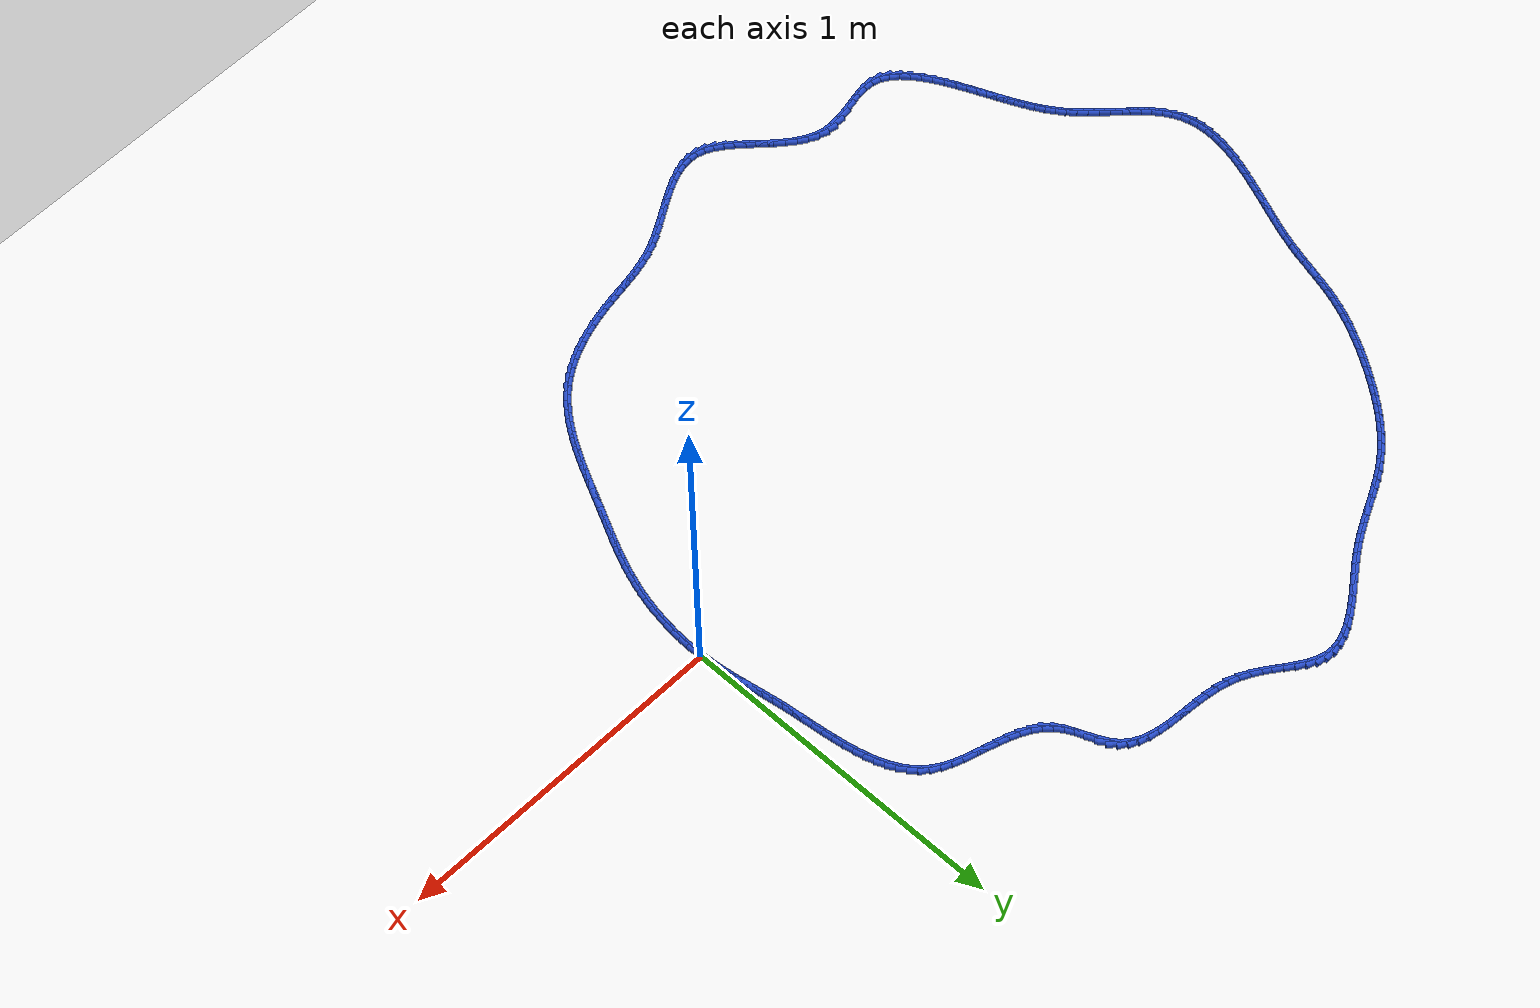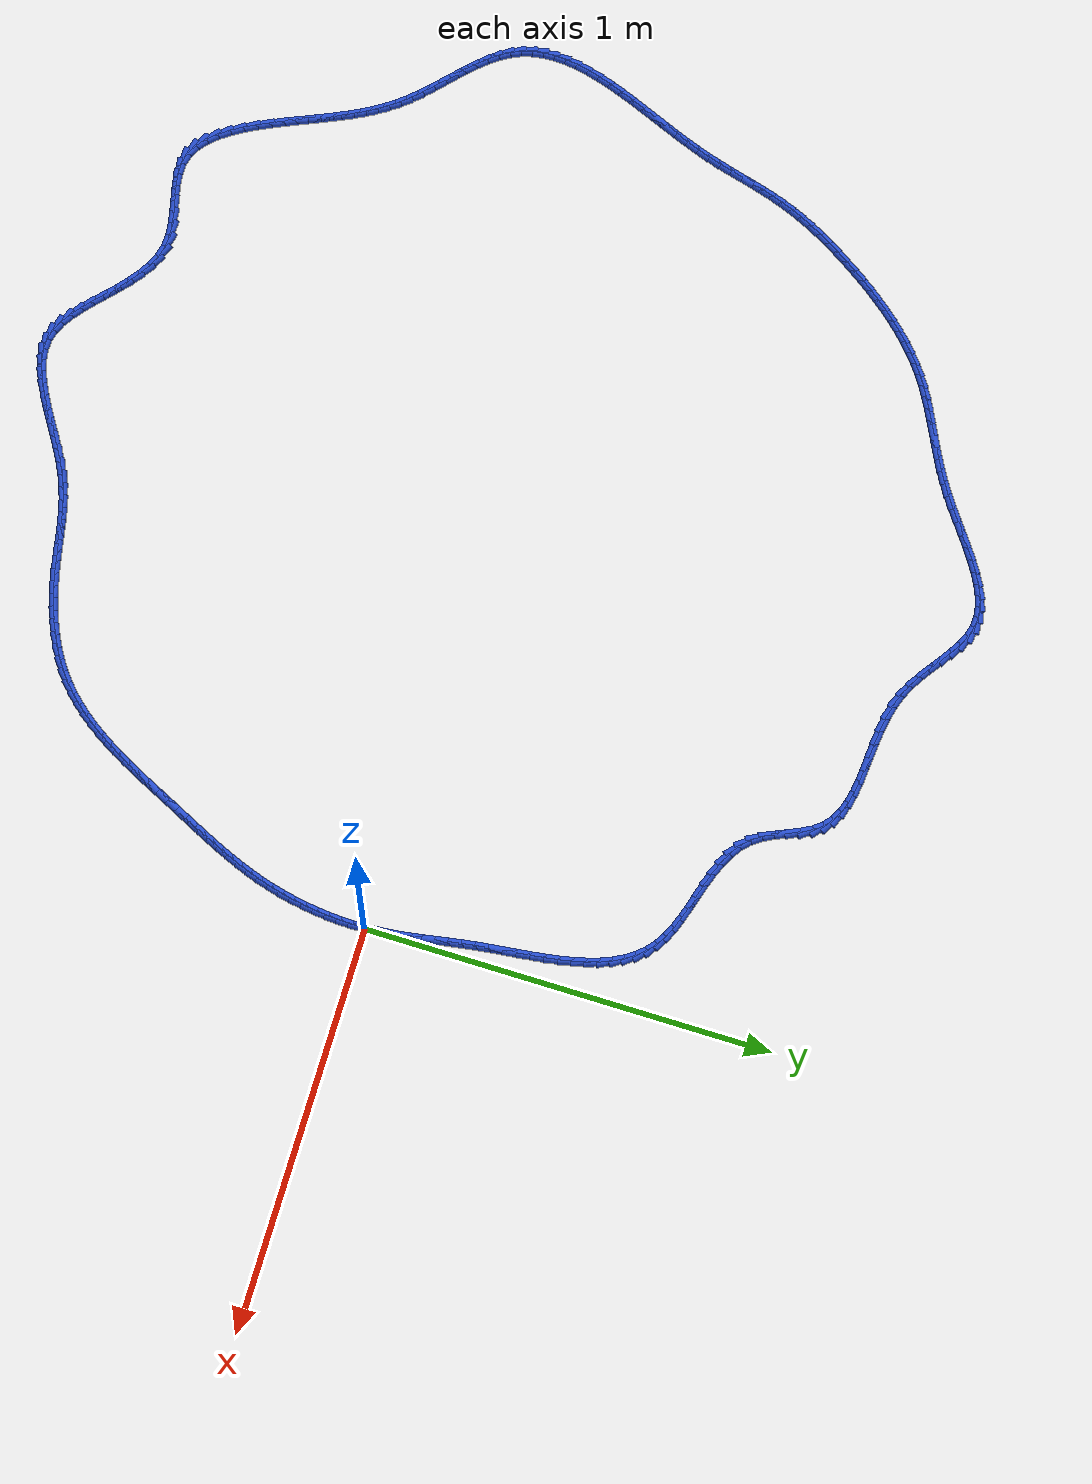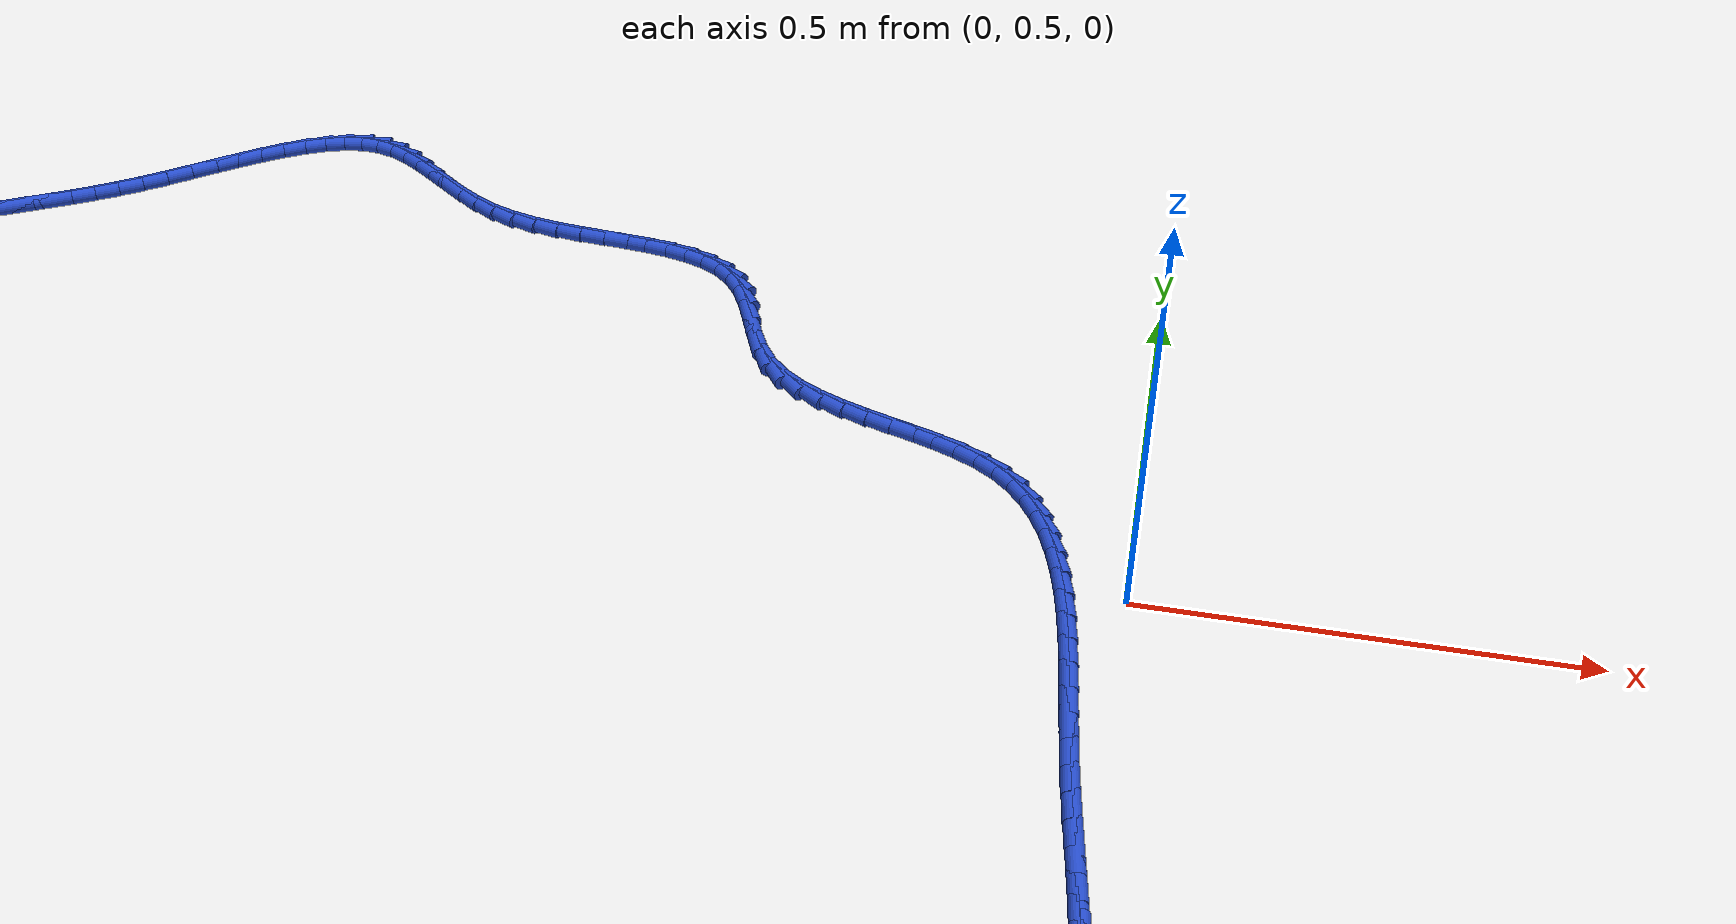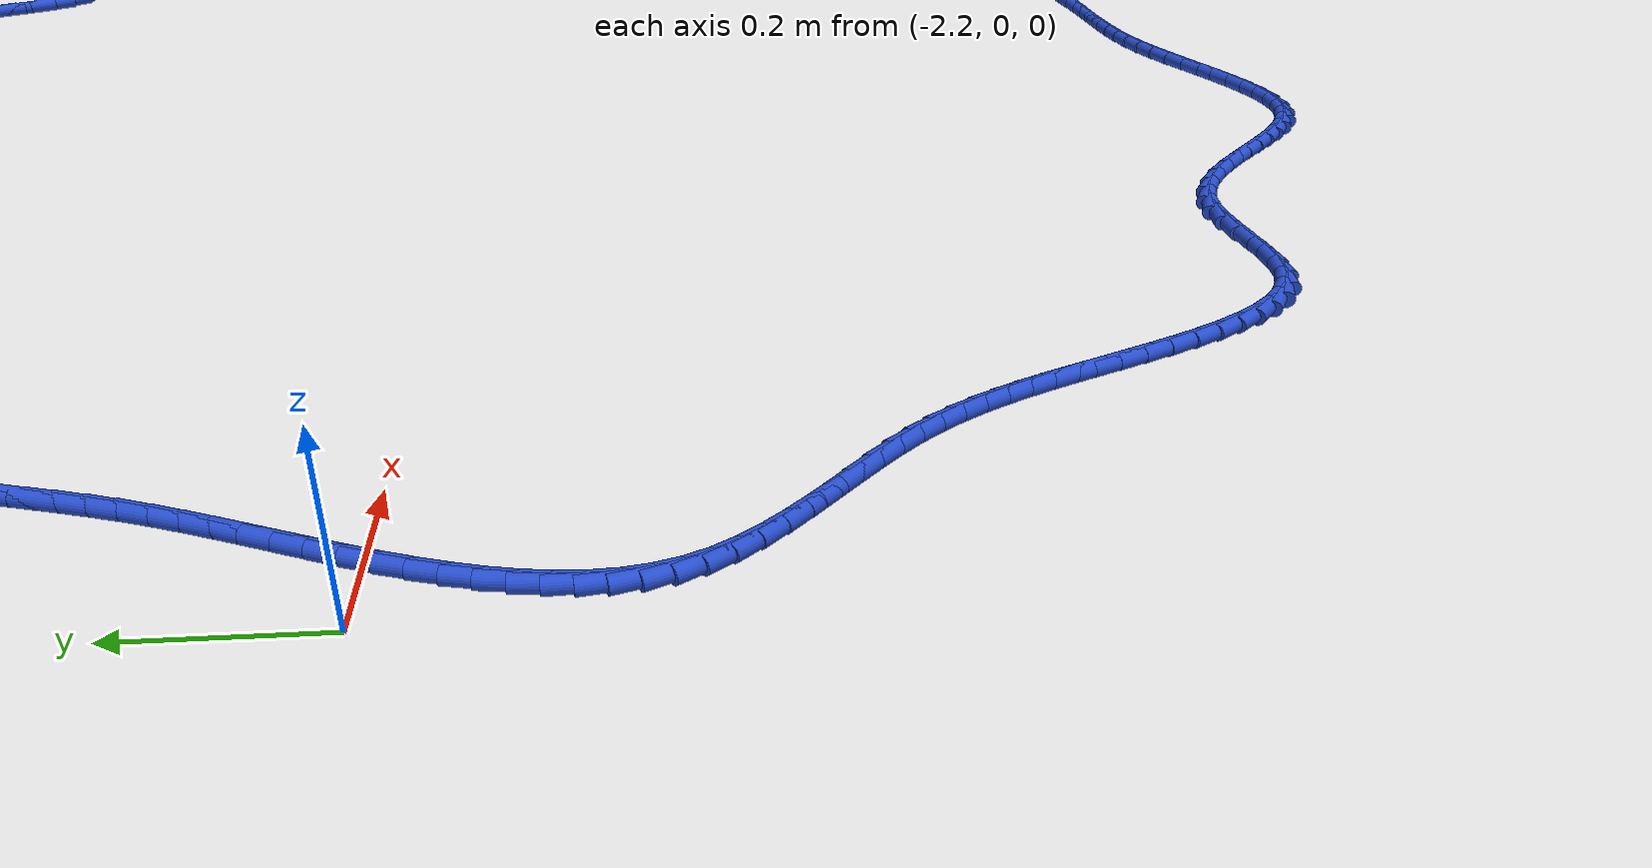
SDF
<sdf version="1.6">
 <world name="default">
  <light name="sun" type="directional">
   <pose>0 0 10 0 -0 0</pose>
   <diffuse>0.8 0.8 0.8 1</diffuse>
   <specular>0.2 0.2 0.2 1</specular>
   <attenuation>
    <range>1000</range>
    <constant>0.9</constant>
    <linear>0.01</linear>
    <quadratic>0.001</quadratic>
   </attenuation>
   <direction>-0.5 0.1 -0.9</direction>
  </light>
  <model name="ground_plane">
   <static>1</static>
   <link name="link">
    <collision name="collision">
     <geometry><plane><normal>0 0 1</normal><size>100 100</size></plane></geometry>
     <surface><friction><ode><mu>100</mu><mu2>50</mu2></ode></friction></surface>
    </collision>
    <visual name="visual">
     <cast_shadows>0</cast_shadows>
     <geometry><plane><normal>0 0 1</normal><size>100 100</size></plane></geometry>
     <material>
      <script><uri>file://media/materials/scripts/gazebo.material</uri><name>Gazebo/WhiteGlow</name></script>
     </material>
    </visual>
   </link>
  </model>
  <gravity>0 0 -9.8</gravity>
  <magnetic_field>6e-06 2.3e-05 -4.2e-05</magnetic_field>
  <atmosphere type="adiabatic"/>
  <physics name="default_physics" default="0" type="ode">
   <max_step_size>0.001</max_step_size>
   <real_time_factor>1</real_time_factor>
   <real_time_update_rate>1000</real_time_update_rate>
  </physics>
  <scene><ambient>0.4 0.4 0.4 1</ambient><background>0.7 0.7 0.7 1</background><shadows>1</shadows></scene>
  <spherical_coordinates>
   <surface_model>EARTH_WGS84</surface_model>
   <latitude_deg>0</latitude_deg>
   <longitude_deg>0</longitude_deg>
   <elevation>0</elevation>
   <heading_deg>0</heading_deg>
  </spherical_coordinates>
  <model name="line">
   <link name="link_0">
    <pose>-3.122502256758253e-17 4.85722573273506e-17 0.01 0 1.57 -1.511353658124917</pose>
    <collision name="collision">
     <geometry><cylinder><radius>0.01</radius><length>0.08</length></cylinder></geometry>
    </collision>
    <visual name="visual">
     <material>
      <script><name>Gazebo/Blue</name><uri>file://media/materials/scripts/gazebo.material</uri></script>
     </material>
     <geometry><cylinder><radius>0.01</radius><length>0.08</length></cylinder></geometry>
    </visual>
   </link>
   <link name="link_1">
    <pose>-0.0017431352190729868 0.02929009904243795 0.01 0 1.57 -1.4755822268999617</pose>
    <collision name="collision">
     <geometry><cylinder><radius>0.01</radius><length>0.08</length></cylinder></geometry>
    </collision>
    <visual name="visual">
     <material>
      <script><name>Gazebo/Blue</name><uri>file://media/materials/scripts/gazebo.material</uri></script>
     </material>
     <geometry><cylinder><radius>0.01</radius><length>0.08</length></cylinder></geometry>
    </visual>
   </link>
   <link name="link_2">
    <pose>-0.0045204153321044774 0.05837069060994985 0.01 0 1.57 -1.4466732365010249</pose>
    <collision name="collision">
     <geometry><cylinder><radius>0.01</radius><length>0.08</length></cylinder></geometry>
    </collision>
    <visual name="visual">
     <material>
      <script><name>Gazebo/Blue</name><uri>file://media/materials/scripts/gazebo.material</uri></script>
     </material>
     <geometry><cylinder><radius>0.01</radius><length>0.08</length></cylinder></geometry>
    </visual>
   </link>
   <link name="link_3">
    <pose>-0.008138639546915962 0.08737112600543553 0.01 0 1.57 -1.4249874915659761</pose>
    <collision name="collision">
     <geometry><cylinder><radius>0.01</radius><length>0.08</length></cylinder></geometry>
    </collision>
    <visual name="visual">
     <material>
      <script><name>Gazebo/Blue</name><uri>file://media/materials/scripts/gazebo.material</uri></script>
     </material>
     <geometry><cylinder><radius>0.01</radius><length>0.08</length></cylinder></geometry>
    </visual>
   </link>
   <link name="link_4">
    <pose>-0.012404607071328878 0.1164207565317946 0.01 0 1.57 -1.4106735322179795</pose>
    <collision name="collision">
     <geometry><cylinder><radius>0.01</radius><length>0.08</length></cylinder></geometry>
    </collision>
    <visual name="visual">
     <material>
      <script><name>Gazebo/Blue</name><uri>file://media/materials/scripts/gazebo.material</uri></script>
     </material>
     <geometry><cylinder><radius>0.01</radius><length>0.08</length></cylinder></geometry>
    </visual>
   </link>
   <link name="link_5">
    <pose>-0.01712511711316468 0.1456489334919269 0.01 0 1.57 -1.4036990282547968</pose>
    <collision name="collision">
     <geometry><cylinder><radius>0.01</radius><length>0.08</length></cylinder></geometry>
    </collision>
    <visual name="visual">
     <material>
      <script><name>Gazebo/Blue</name><uri>file://media/materials/scripts/gazebo.material</uri></script>
     </material>
     <geometry><cylinder><radius>0.01</radius><length>0.08</length></cylinder></geometry>
    </visual>
   </link>
   <link name="link_6">
    <pose>-0.022106968880244795 0.1751850081887319 0.01 0 1.57 -1.4038810192795896</pose>
    <collision name="collision">
     <geometry><cylinder><radius>0.01</radius><length>0.08</length></cylinder></geometry>
    </collision>
    <visual name="visual">
     <material>
      <script><name>Gazebo/Blue</name><uri>file://media/materials/scripts/gazebo.material</uri></script>
     </material>
     <geometry><cylinder><radius>0.01</radius><length>0.08</length></cylinder></geometry>
    </visual>
   </link>
   <link name="link_7">
    <pose>-0.027156961580390684 0.20515833192510952 0.01 0 1.57 -1.4109106931963644</pose>
    <collision name="collision">
     <geometry><cylinder><radius>0.01</radius><length>0.08</length></cylinder></geometry>
    </collision>
    <visual name="visual">
     <material>
      <script><name>Gazebo/Blue</name><uri>file://media/materials/scripts/gazebo.material</uri></script>
     </material>
     <geometry><cylinder><radius>0.01</radius><length>0.08</length></cylinder></geometry>
    </visual>
   </link>
   <link name="link_8">
    <pose>-0.032081894421423764 0.23569825600395922 0.01 0 1.57 -1.4243716691834938</pose>
    <collision name="collision">
     <geometry><cylinder><radius>0.01</radius><length>0.08</length></cylinder></geometry>
    </collision>
    <visual name="visual">
     <material>
      <script><name>Gazebo/Blue</name><uri>file://media/materials/scripts/gazebo.material</uri></script>
     </material>
     <geometry><cylinder><radius>0.01</radius><length>0.08</length></cylinder></geometry>
    </visual>
   </link>
   <link name="link_9">
    <pose>-0.03668856661116552 0.266934131728181 0.01 0 1.57 -1.441789835447863</pose>
    <collision name="collision">
     <geometry><cylinder><radius>0.01</radius><length>0.08</length></cylinder></geometry>
    </collision>
    <visual name="visual">
     <material>
      <script><name>Gazebo/Blue</name><uri>file://media/materials/scripts/gazebo.material</uri></script>
     </material>
     <geometry><cylinder><radius>0.01</radius><length>0.08</length></cylinder></geometry>
    </visual>
   </link>
   <link name="link_10">
    <pose>-0.04084113952948911 0.29894423164617806 0.01 0 1.57 -1.4527999926948498</pose>
    <collision name="collision">
     <geometry><cylinder><radius>0.01</radius><length>0.08</length></cylinder></geometry>
    </collision>
    <visual name="visual">
     <material>
      <script><name>Gazebo/Blue</name><uri>file://media/materials/scripts/gazebo.material</uri></script>
     </material>
     <geometry><cylinder><radius>0.01</radius><length>0.08</length></cylinder></geometry>
    </visual>
   </link>
   <link name="link_11">
    <pose>-0.044705094869415735 0.3315385144376585 0.01 0 1.57 -1.4546244826638184</pose>
    <collision name="collision">
     <geometry><cylinder><radius>0.01</radius><length>0.08</length></cylinder></geometry>
    </collision>
    <visual name="visual">
     <material>
      <script><name>Gazebo/Blue</name><uri>file://media/materials/scripts/gazebo.material</uri></script>
     </material>
     <geometry><cylinder><radius>0.01</radius><length>0.08</length></cylinder></geometry>
    </visual>
   </link>
   <link name="link_12">
    <pose>-0.048544509331606166 0.36443914381206227 0.01 0 1.57 -1.447551700593808</pose>
    <collision name="collision">
     <geometry><cylinder><radius>0.01</radius><length>0.08</length></cylinder></geometry>
    </collision>
    <visual name="visual">
     <material>
      <script><name>Gazebo/Blue</name><uri>file://media/materials/scripts/gazebo.material</uri></script>
     </material>
     <geometry><cylinder><radius>0.01</radius><length>0.08</length></cylinder></geometry>
    </visual>
   </link>
   <link name="link_13">
    <pose>-0.05262351593717284 0.39736823332768606 0.01 0 1.57 -1.4314729352384303</pose>
    <collision name="collision">
     <geometry><cylinder><radius>0.01</radius><length>0.08</length></cylinder></geometry>
    </collision>
    <visual name="visual">
     <material>
      <script><name>Gazebo/Blue</name><uri>file://media/materials/scripts/gazebo.material</uri></script>
     </material>
     <geometry><cylinder><radius>0.01</radius><length>0.08</length></cylinder></geometry>
    </visual>
   </link>
   <link name="link_14">
    <pose>-0.057206247707228174 0.43004789654282655 0.01 0 1.57 -1.4058938391447775</pose>
    <collision name="collision">
     <geometry><cylinder><radius>0.01</radius><length>0.08</length></cylinder></geometry>
    </collision>
    <visual name="visual">
     <material>
      <script><name>Gazebo/Blue</name><uri>file://media/materials/scripts/gazebo.material</uri></script>
     </material>
     <geometry><cylinder><radius>0.01</radius><length>0.08</length></cylinder></geometry>
    </visual>
   </link>
   <link name="link_15">
    <pose>-0.06255683766288461 0.46220024701578033 0.01 0 1.57 -1.3699324122369962</pose>
    <collision name="collision">
     <geometry><cylinder><radius>0.01</radius><length>0.08</length></cylinder></geometry>
    </collision>
    <visual name="visual">
     <material>
      <script><name>Gazebo/Blue</name><uri>file://media/materials/scripts/gazebo.material</uri></script>
     </material>
     <geometry><cylinder><radius>0.01</radius><length>0.08</length></cylinder></geometry>
    </visual>
   </link>
   <link name="link_16">
    <pose>-0.0689394188252546 0.4935473983048441 0.01 0 1.57 -1.3223162524967749</pose>
    <collision name="collision">
     <geometry><cylinder><radius>0.01</radius><length>0.08</length></cylinder></geometry>
    </collision>
    <visual name="visual">
     <material>
      <script><name>Gazebo/Blue</name><uri>file://media/materials/scripts/gazebo.material</uri></script>
     </material>
     <geometry><cylinder><radius>0.01</radius><length>0.08</length></cylinder></geometry>
    </visual>
   </link>
   <link name="link_17">
    <pose>-0.07661812421545054 0.5238114639683142 0.01 0 1.57 -1.2614081170068991</pose>
    <collision name="collision">
     <geometry><cylinder><radius>0.01</radius><length>0.08</length></cylinder></geometry>
    </collision>
    <visual name="visual">
     <material>
      <script><name>Gazebo/Blue</name><uri>file://media/materials/scripts/gazebo.material</uri></script>
     </material>
     <geometry><cylinder><radius>0.01</radius><length>0.08</length></cylinder></geometry>
    </visual>
   </link>
   <link name="link_18">
    <pose>-0.08585708685458489 0.552714557564488 0.01 0 1.57 -1.185314888725097</pose>
    <collision name="collision">
     <geometry><cylinder><radius>0.01</radius><length>0.08</length></cylinder></geometry>
    </collision>
    <visual name="visual">
     <material>
      <script><name>Gazebo/Blue</name><uri>file://media/materials/scripts/gazebo.material</uri></script>
     </material>
     <geometry><cylinder><radius>0.01</radius><length>0.08</length></cylinder></geometry>
    </visual>
   </link>
   <link name="link_19">
    <pose>-0.09692043976377004 0.5799787926516613 0.01 0 1.57 -1.0921724006722007</pose>
    <collision name="collision">
     <geometry><cylinder><radius>0.01</radius><length>0.08</length></cylinder></geometry>
    </collision>
    <visual name="visual">
     <material>
      <script><name>Gazebo/Blue</name><uri>file://media/materials/scripts/gazebo.material</uri></script>
     </material>
     <geometry><cylinder><radius>0.01</radius><length>0.08</length></cylinder></geometry>
    </visual>
   </link>
   <link name="link_20">
    <pose>-0.11007231596411846 0.6053262827881312 0.01 0 1.57 -0.9807246017821325</pose>
    <collision name="collision">
     <geometry><cylinder><radius>0.01</radius><length>0.08</length></cylinder></geometry>
    </collision>
    <visual name="visual">
     <material>
      <script><name>Gazebo/Blue</name><uri>file://media/materials/scripts/gazebo.material</uri></script>
     </material>
     <geometry><cylinder><radius>0.01</radius><length>0.08</length></cylinder></geometry>
    </visual>
   </link>
   <link name="link_21">
    <pose>-0.1255768484767426 0.6284791415321941 0.01 0 1.57 -0.8512540655399563</pose>
    <collision name="collision">
     <geometry><cylinder><radius>0.01</radius><length>0.08</length></cylinder></geometry>
    </collision>
    <visual name="visual">
     <material>
      <script><name>Gazebo/Blue</name><uri>file://media/materials/scripts/gazebo.material</uri></script>
     </material>
     <geometry><cylinder><radius>0.01</radius><length>0.08</length></cylinder></geometry>
    </visual>
   </link>
   <link name="link_22">
    <pose>-0.14369817032275484 0.6491594824421467 0.01 0 1.57 -0.7066470209463559</pose>
    <collision name="collision">
     <geometry><cylinder><radius>0.01</radius><length>0.08</length></cylinder></geometry>
    </collision>
    <visual name="visual">
     <material>
      <script><name>Gazebo/Blue</name><uri>file://media/materials/scripts/gazebo.material</uri></script>
     </material>
     <geometry><cylinder><radius>0.01</radius><length>0.08</length></cylinder></geometry>
    </visual>
   </link>
   <link name="link_23">
    <pose>-0.16470041452326764 0.6670894190762858 0.01 0 1.57 -0.5587662865493092</pose>
    <collision name="collision">
     <geometry><cylinder><radius>0.01</radius><length>0.08</length></cylinder></geometry>
    </collision>
    <visual name="visual">
     <material>
      <script><name>Gazebo/Blue</name><uri>file://media/materials/scripts/gazebo.material</uri></script>
     </material>
     <geometry><cylinder><radius>0.01</radius><length>0.08</length></cylinder></geometry>
    </visual>
   </link>
   <link name="link_24">
    <pose>-0.18872933492028682 0.6821130742859268 0.01 0 1.57 -0.4416547844708237</pose>
    <collision name="collision">
     <geometry><cylinder><radius>0.01</radius><length>0.08</length></cylinder></geometry>
    </collision>
    <visual name="visual">
     <material>
      <script><name>Gazebo/Blue</name><uri>file://media/materials/scripts/gazebo.material</uri></script>
     </material>
     <geometry><cylinder><radius>0.01</radius><length>0.08</length></cylinder></geometry>
    </visual>
   </link>
   <link name="link_25">
    <pose>-0.2153324680510525 0.6946911326436002 0.01 0 1.57 -0.36142009280151555</pose>
    <collision name="collision">
     <geometry><cylinder><radius>0.01</radius><length>0.08</length></cylinder></geometry>
    </collision>
    <visual name="visual">
     <material>
      <script><name>Gazebo/Blue</name><uri>file://media/materials/scripts/gazebo.material</uri></script>
     </material>
     <geometry><cylinder><radius>0.01</radius><length>0.08</length></cylinder></geometry>
    </visual>
   </link>
   <link name="link_26">
    <pose>-0.24386882220752884 0.705478588211849 0.01 0 1.57 -0.3129473092655493</pose>
    <collision name="collision">
     <geometry><cylinder><radius>0.01</radius><length>0.08</length></cylinder></geometry>
    </collision>
    <visual name="visual">
     <material>
      <script><name>Gazebo/Blue</name><uri>file://media/materials/scripts/gazebo.material</uri></script>
     </material>
     <geometry><cylinder><radius>0.01</radius><length>0.08</length></cylinder></geometry>
    </visual>
   </link>
   <link name="link_27">
    <pose>-0.27369733504160443 0.7151305078594778 0.01 0 1.57 -0.2922863754003836</pose>
    <collision name="collision">
     <geometry><cylinder><radius>0.01</radius><length>0.08</length></cylinder></geometry>
    </collision>
    <visual name="visual">
     <material>
      <script><name>Gazebo/Blue</name><uri>file://media/materials/scripts/gazebo.material</uri></script>
     </material>
     <geometry><cylinder><radius>0.01</radius><length>0.08</length></cylinder></geometry>
    </visual>
   </link>
   <link name="link_28">
    <pose>-0.3041769442051682 0.7243019584552928 0.01 0 1.57 -0.2974385430829808</pose>
    <collision name="collision">
     <geometry><cylinder><radius>0.01</radius><length>0.08</length></cylinder></geometry>
    </collision>
    <visual name="visual">
     <material>
      <script><name>Gazebo/Blue</name><uri>file://media/materials/scripts/gazebo.material</uri></script>
     </material>
     <geometry><cylinder><radius>0.01</radius><length>0.08</length></cylinder></geometry>
    </visual>
   </link>
   <link name="link_29">
    <pose>-0.334666587350109 0.7336480068680986 0.01 0 1.57 -0.3284523495971984</pose>
    <collision name="collision">
     <geometry><cylinder><radius>0.01</radius><length>0.08</length></cylinder></geometry>
    </collision>
    <visual name="visual">
     <material>
      <script><name>Gazebo/Blue</name><uri>file://media/materials/scripts/gazebo.material</uri></script>
     </material>
     <geometry><cylinder><radius>0.01</radius><length>0.08</length></cylinder></geometry>
    </visual>
   </link>
   <link name="link_30">
    <pose>-0.36452520212831585 0.743823719966701 0.01 0 1.57 -0.3872981602120869</pose>
    <collision name="collision">
     <geometry><cylinder><radius>0.01</radius><length>0.08</length></cylinder></geometry>
    </collision>
    <visual name="visual">
     <material>
      <script><name>Gazebo/Blue</name><uri>file://media/materials/scripts/gazebo.material</uri></script>
     </material>
     <geometry><cylinder><radius>0.01</radius><length>0.08</length></cylinder></geometry>
    </visual>
   </link>
   <link name="link_31">
    <pose>-0.39311172619167734 0.7554841646199053 0.01 0 1.57 -0.4774539808486102</pose>
    <collision name="collision">
     <geometry><cylinder><radius>0.01</radius><length>0.08</length></cylinder></geometry>
    </collision>
    <visual name="visual">
     <material>
      <script><name>Gazebo/Blue</name><uri>file://media/materials/scripts/gazebo.material</uri></script>
     </material>
     <geometry><cylinder><radius>0.01</radius><length>0.08</length></cylinder></geometry>
    </visual>
   </link>
   <link name="link_32">
    <pose>-0.41978509719208246 0.7692844076965165 0.01 0 1.57 -0.602658568605454</pose>
    <collision name="collision">
     <geometry><cylinder><radius>0.01</radius><length>0.08</length></cylinder></geometry>
    </collision>
    <visual name="visual">
     <material>
      <script><name>Gazebo/Blue</name><uri>file://media/materials/scripts/gazebo.material</uri></script>
     </material>
     <geometry><cylinder><radius>0.01</radius><length>0.08</length></cylinder></geometry>
    </visual>
   </link>
   <link name="link_33">
    <pose>-0.4439042527814202 0.7858795160653407 0.01 0 1.57 -0.7639501347197892</pose>
    <collision name="collision">
     <geometry><cylinder><radius>0.01</radius><length>0.08</length></cylinder></geometry>
    </collision>
    <visual name="visual">
     <material>
      <script><name>Gazebo/Blue</name><uri>file://media/materials/scripts/gazebo.material</uri></script>
     </material>
     <geometry><cylinder><radius>0.01</radius><length>0.08</length></cylinder></geometry>
    </visual>
   </link>
   <link name="link_34">
    <pose>-0.46482813061157907 0.8059245565951821 0.01 0 1.57 -0.9504901798072123</pose>
    <collision name="collision">
     <geometry><cylinder><radius>0.01</radius><length>0.08</length></cylinder></geometry>
    </collision>
    <visual name="visual">
     <material>
      <script><name>Gazebo/Blue</name><uri>file://media/materials/scripts/gazebo.material</uri></script>
     </material>
     <geometry><cylinder><radius>0.01</radius><length>0.08</length></cylinder></geometry>
    </visual>
   </link>
   <link name="link_35">
    <pose>-0.48200562203535996 0.8299701638669684 0.01 0 1.57 -1.0935989798500274</pose>
    <collision name="collision">
     <geometry><cylinder><radius>0.01</radius><length>0.08</length></cylinder></geometry>
    </collision>
    <visual name="visual">
     <material>
      <script><name>Gazebo/Blue</name><uri>file://media/materials/scripts/gazebo.material</uri></script>
     </material>
     <geometry><cylinder><radius>0.01</radius><length>0.08</length></cylinder></geometry>
    </visual>
   </link>
   <link name="link_36">
    <pose>-0.4960767192298586 0.8571841568252043 0.01 0 1.57 -1.1598960382296277</pose>
    <collision name="collision">
     <geometry><cylinder><radius>0.01</radius><length>0.08</length></cylinder></geometry>
    </collision>
    <visual name="visual">
     <material>
      <script><name>Gazebo/Blue</name><uri>file://media/materials/scripts/gazebo.material</uri></script>
     </material>
     <geometry><cylinder><radius>0.01</radius><length>0.08</length></cylinder></geometry>
    </visual>
   </link>
   <link name="link_37">
    <pose>-0.508525057934264 0.885754921367725 0.01 0 1.57 -1.1573278387355874</pose>
    <collision name="collision">
     <geometry><cylinder><radius>0.01</radius><length>0.08</length></cylinder></geometry>
    </collision>
    <visual name="visual">
     <material>
      <script><name>Gazebo/Blue</name><uri>file://media/materials/scripts/gazebo.material</uri></script>
     </material>
     <geometry><cylinder><radius>0.01</radius><length>0.08</length></cylinder></geometry>
    </visual>
   </link>
   <link name="link_38">
    <pose>-0.520852134341846 0.9138501081912198 0.01 0 1.57 -1.0822256443290847</pose>
    <collision name="collision">
     <geometry><cylinder><radius>0.01</radius><length>0.08</length></cylinder></geometry>
    </collision>
    <visual name="visual">
     <material>
      <script><name>Gazebo/Blue</name><uri>file://media/materials/scripts/gazebo.material</uri></script>
     </material>
     <geometry><cylinder><radius>0.01</radius><length>0.08</length></cylinder></geometry>
    </visual>
   </link>
   <link name="link_39">
    <pose>-0.5345594446458743 0.9396373679923788 0.01 0 1.57 -0.9182252649341252</pose>
    <collision name="collision">
     <geometry><cylinder><radius>0.01</radius><length>0.08</length></cylinder></geometry>
    </collision>
    <visual name="visual">
     <material>
      <script><name>Gazebo/Blue</name><uri>file://media/materials/scripts/gazebo.material</uri></script>
     </material>
     <geometry><cylinder><radius>0.01</radius><length>0.08</length></cylinder></geometry>
    </visual>
   </link>
   <link name="link_40">
    <pose>-0.5511261184801582 0.9613138565300912 0.01 0 1.57 -0.697713694980659</pose>
    <collision name="collision">
     <geometry><cylinder><radius>0.01</radius><length>0.08</length></cylinder></geometry>
    </collision>
    <visual name="visual">
     <material>
      <script><name>Gazebo/Blue</name><uri>file://media/materials/scripts/gazebo.material</uri></script>
     </material>
     <geometry><cylinder><radius>0.01</radius><length>0.08</length></cylinder></geometry>
    </visual>
   </link>
   <link name="link_41">
    <pose>-0.5712138021008802 0.9781551206294322 0.01 0 1.57 -0.4983171802083048</pose>
    <collision name="collision">
     <geometry><cylinder><radius>0.01</radius><length>0.08</length></cylinder></geometry>
    </collision>
    <visual name="visual">
     <material>
      <script><name>Gazebo/Blue</name><uri>file://media/materials/scripts/gazebo.material</uri></script>
     </material>
     <geometry><cylinder><radius>0.01</radius><length>0.08</length></cylinder></geometry>
    </visual>
   </link>
   <link name="link_42">
    <pose>-0.5944513511023222 0.9907991228581307 0.01 0 1.57 -0.33974240535872896</pose>
    <collision name="collision">
     <geometry><cylinder><radius>0.01</radius><length>0.08</length></cylinder></geometry>
    </collision>
    <visual name="visual">
     <material>
      <script><name>Gazebo/Blue</name><uri>file://media/materials/scripts/gazebo.material</uri></script>
     </material>
     <geometry><cylinder><radius>0.01</radius><length>0.08</length></cylinder></geometry>
    </visual>
   </link>
   <link name="link_43">
    <pose>-0.6204014539082907 0.999971110843731 0.01 0 1.57 -0.22382593608973778</pose>
    <collision name="collision">
     <geometry><cylinder><radius>0.01</radius><length>0.08</length></cylinder></geometry>
    </collision>
    <visual name="visual">
     <material>
      <script><name>Gazebo/Blue</name><uri>file://media/materials/scripts/gazebo.material</uri></script>
     </material>
     <geometry><cylinder><radius>0.01</radius><length>0.08</length></cylinder></geometry>
    </visual>
   </link>
   <link name="link_44">
    <pose>-0.6486267989425929 1.006396332213779 0.01 0 1.57 -0.1454467392183148</pose>
    <collision name="collision">
     <geometry><cylinder><radius>0.01</radius><length>0.08</length></cylinder></geometry>
    </collision>
    <visual name="visual">
     <material>
      <script><name>Gazebo/Blue</name><uri>file://media/materials/scripts/gazebo.material</uri></script>
     </material>
     <geometry><cylinder><radius>0.01</radius><length>0.08</length></cylinder></geometry>
    </visual>
   </link>
   <link name="link_45">
    <pose>-0.6786900746290351 1.010800034595819 0.01 0 1.57 -0.09844256660133281</pose>
    <collision name="collision">
     <geometry><cylinder><radius>0.01</radius><length>0.08</length></cylinder></geometry>
    </collision>
    <visual name="visual">
     <material>
      <script><name>Gazebo/Blue</name><uri>file://media/materials/scripts/gazebo.material</uri></script>
     </material>
     <geometry><cylinder><radius>0.01</radius><length>0.08</length></cylinder></geometry>
    </visual>
   </link>
   <link name="link_46">
    <pose>-0.7101539693914242 1.0139074656173959 0.01 0 1.57 -0.07805957110505754</pose>
    <collision name="collision">
     <geometry><cylinder><radius>0.01</radius><length>0.08</length></cylinder></geometry>
    </collision>
    <visual name="visual">
     <material>
      <script><name>Gazebo/Blue</name><uri>file://media/materials/scripts/gazebo.material</uri></script>
     </material>
     <geometry><cylinder><radius>0.01</radius><length>0.08</length></cylinder></geometry>
    </visual>
   </link>
   <link name="link_47">
    <pose>-0.7425811716535667 1.016443872906055 0.01 0 1.57 -0.08146935330045363</pose>
    <collision name="collision">
     <geometry><cylinder><radius>0.01</radius><length>0.08</length></cylinder></geometry>
    </collision>
    <visual name="visual">
     <material>
      <script><name>Gazebo/Blue</name><uri>file://media/materials/scripts/gazebo.material</uri></script>
     </material>
     <geometry><cylinder><radius>0.01</radius><length>0.08</length></cylinder></geometry>
    </visual>
   </link>
   <link name="link_48">
    <pose>-0.7755343698392695 1.019134504089341 0.01 0 1.57 -0.10763025873868412</pose>
    <collision name="collision">
     <geometry><cylinder><radius>0.01</radius><length>0.08</length></cylinder></geometry>
    </collision>
    <visual name="visual">
     <material>
      <script><name>Gazebo/Blue</name><uri>file://media/materials/scripts/gazebo.material</uri></script>
     </material>
     <geometry><cylinder><radius>0.01</radius><length>0.08</length></cylinder></geometry>
    </visual>
   </link>
   <link name="link_49">
    <pose>-0.8085762523723394 1.0227046067947991 0.01 0 1.57 -0.15698172734042742</pose>
    <collision name="collision">
     <geometry><cylinder><radius>0.01</radius><length>0.08</length></cylinder></geometry>
    </collision>
    <visual name="visual">
     <material>
      <script><name>Gazebo/Blue</name><uri>file://media/materials/scripts/gazebo.material</uri></script>
     </material>
     <geometry><cylinder><radius>0.01</radius><length>0.08</length></cylinder></geometry>
    </visual>
   </link>
   <link name="link_50">
    <pose>-0.8412695076765828 1.0278794286499742 0.01 0 1.57 -0.23100706201490087</pose>
    <collision name="collision">
     <geometry><cylinder><radius>0.01</radius><length>0.08</length></cylinder></geometry>
    </collision>
    <visual name="visual">
     <material>
      <script><name>Gazebo/Blue</name><uri>file://media/materials/scripts/gazebo.material</uri></script>
     </material>
     <geometry><cylinder><radius>0.01</radius><length>0.08</length></cylinder></geometry>
    </visual>
   </link>
   <link name="link_51">
    <pose>-0.8731768241758071 1.0353842172824113 0.01 0 1.57 -0.3314561421136073</pose>
    <collision name="collision">
     <geometry><cylinder><radius>0.01</radius><length>0.08</length></cylinder></geometry>
    </collision>
    <visual name="visual">
     <material>
      <script><name>Gazebo/Blue</name><uri>file://media/materials/scripts/gazebo.material</uri></script>
     </material>
     <geometry><cylinder><radius>0.01</radius><length>0.08</length></cylinder></geometry>
    </visual>
   </link>
   <link name="link_52">
    <pose>-0.9038608902938181 1.045944220319655 0.01 0 1.57 -0.4488613184978638</pose>
    <collision name="collision">
     <geometry><cylinder><radius>0.01</radius><length>0.08</length></cylinder></geometry>
    </collision>
    <visual name="visual">
     <material>
      <script><name>Gazebo/Blue</name><uri>file://media/materials/scripts/gazebo.material</uri></script>
     </material>
     <geometry><cylinder><radius>0.01</radius><length>0.08</length></cylinder></geometry>
    </visual>
   </link>
   <link name="link_53">
    <pose>-0.9329962437421928 1.0599773056451225 0.01 0 1.57 -0.5405208021389962</pose>
    <collision name="collision">
     <geometry><cylinder><radius>0.01</radius><length>0.08</length></cylinder></geometry>
    </collision>
    <visual name="visual">
     <material>
      <script><name>Gazebo/Blue</name><uri>file://media/materials/scripts/gazebo.material</uri></script>
     </material>
     <geometry><cylinder><radius>0.01</radius><length>0.08</length></cylinder></geometry>
    </visual>
   </link>
   <link name="link_54">
    <pose>-0.9607243975339237 1.0766180182751295 0.01 0 1.57 -0.5964221918145656</pose>
    <collision name="collision">
     <geometry><cylinder><radius>0.01</radius><length>0.08</length></cylinder></geometry>
    </collision>
    <visual name="visual">
     <material>
      <script><name>Gazebo/Blue</name><uri>file://media/materials/scripts/gazebo.material</uri></script>
     </material>
     <geometry><cylinder><radius>0.01</radius><length>0.08</length></cylinder></geometry>
    </visual>
   </link>
   <link name="link_55">
    <pose>-0.9873087153436709 1.0946660381056839 0.01 0 1.57 -0.6175423319244921</pose>
    <collision name="collision">
     <geometry><cylinder><radius>0.01</radius><length>0.08</length></cylinder></geometry>
    </collision>
    <visual name="visual">
     <material>
      <script><name>Gazebo/Blue</name><uri>file://media/materials/scripts/gazebo.material</uri></script>
     </material>
     <geometry><cylinder><radius>0.01</radius><length>0.08</length></cylinder></geometry>
    </visual>
   </link>
   <link name="link_56">
    <pose>-1.0130125611857852 1.112921044099273 0.01 0 1.57 -0.6026807748835207</pose>
    <collision name="collision">
     <geometry><cylinder><radius>0.01</radius><length>0.08</length></cylinder></geometry>
    </collision>
    <visual name="visual">
     <material>
      <script><name>Gazebo/Blue</name><uri>file://media/materials/scripts/gazebo.material</uri></script>
     </material>
     <geometry><cylinder><radius>0.01</radius><length>0.08</length></cylinder></geometry>
    </visual>
   </link>
   <link name="link_57">
    <pose>-1.0380992990746158 1.1301827152183828 0.01 0 1.57 -0.5471766713011936</pose>
    <collision name="collision">
     <geometry><cylinder><radius>0.01</radius><length>0.08</length></cylinder></geometry>
    </collision>
    <visual name="visual">
     <material>
      <script><name>Gazebo/Blue</name><uri>file://media/materials/scripts/gazebo.material</uri></script>
     </material>
     <geometry><cylinder><radius>0.01</radius><length>0.08</length></cylinder></geometry>
    </visual>
   </link>
   <link name="link_58">
    <pose>-1.0628322930245138 1.1452507304255004 0.01 0 1.57 -0.4424146933022829</pose>
    <collision name="collision">
     <geometry><cylinder><radius>0.01</radius><length>0.08</length></cylinder></geometry>
    </collision>
    <visual name="visual">
     <material>
      <script><name>Gazebo/Blue</name><uri>file://media/materials/scripts/gazebo.material</uri></script>
     </material>
     <geometry><cylinder><radius>0.01</radius><length>0.08</length></cylinder></geometry>
    </visual>
   </link>
   <link name="link_59">
    <pose>-1.0874749070498286 1.1569247686831123 0.01 0 1.57 -0.277911214962415</pose>
    <collision name="collision">
     <geometry><cylinder><radius>0.01</radius><length>0.08</length></cylinder></geometry>
    </collision>
    <visual name="visual">
     <material>
      <script><name>Gazebo/Blue</name><uri>file://media/materials/scripts/gazebo.material</uri></script>
     </material>
     <geometry><cylinder><radius>0.01</radius><length>0.08</length></cylinder></geometry>
    </visual>
   </link>
   <link name="link_60">
    <pose>-1.1122905043282565 1.1640045141240842 0.01 0 1.57 -0.06423694749596144</pose>
    <collision name="collision">
     <geometry><cylinder><radius>0.01</radius><length>0.08</length></cylinder></geometry>
    </collision>
    <visual name="visual">
     <material>
      <script><name>Gazebo/Blue</name><uri>file://media/materials/scripts/gazebo.material</uri></script>
     </material>
     <geometry><cylinder><radius>0.01</radius><length>0.08</length></cylinder></geometry>
    </visual>
   </link>
   <link name="link_61">
    <pose>-1.1374881243011514 1.1656253623436648 0.01 0 1.57 0.13435719527198273</pose>
    <collision name="collision">
     <geometry><cylinder><radius>0.01</radius><length>0.08</length></cylinder></geometry>
    </collision>
    <visual name="visual">
     <material>
      <script><name>Gazebo/Blue</name><uri>file://media/materials/scripts/gazebo.material</uri></script>
     </material>
     <geometry><cylinder><radius>0.01</radius><length>0.08</length></cylinder></geometry>
    </visual>
   </link>
   <link name="link_62">
    <pose>-1.1630755117503349 1.162166675738191 0.01 0 1.57 0.29461252777238905</pose>
    <collision name="collision">
     <geometry><cylinder><radius>0.01</radius><length>0.08</length></cylinder></geometry>
    </collision>
    <visual name="visual">
     <material>
      <script><name>Gazebo/Blue</name><uri>file://media/materials/scripts/gazebo.material</uri></script>
     </material>
     <geometry><cylinder><radius>0.01</radius><length>0.08</length></cylinder></geometry>
    </visual>
   </link>
   <link name="link_63">
    <pose>-1.1890137973425283 1.1542958840167838 0.01 0 1.57 0.41658998567926514</pose>
    <collision name="collision">
     <geometry><cylinder><radius>0.01</radius><length>0.08</length></cylinder></geometry>
    </collision>
    <visual name="visual">
     <material>
      <script><name>Gazebo/Blue</name><uri>file://media/materials/scripts/gazebo.material</uri></script>
     </material>
     <geometry><cylinder><radius>0.01</radius><length>0.08</length></cylinder></geometry>
    </visual>
   </link>
   <link name="link_64">
    <pose>-1.2152641117444507 1.1426804168885643 0.01 0 1.57 0.50587177587055</pose>
    <collision name="collision">
     <geometry><cylinder><radius>0.01</radius><length>0.08</length></cylinder></geometry>
    </collision>
    <visual name="visual">
     <material>
      <script><name>Gazebo/Blue</name><uri>file://media/materials/scripts/gazebo.material</uri></script>
     </material>
     <geometry><cylinder><radius>0.01</radius><length>0.08</length></cylinder></geometry>
    </visual>
   </link>
   <link name="link_65">
    <pose>-1.2417875856228229 1.127987704062653 0.01 0 1.57 0.5687180148806973</pose>
    <collision name="collision">
     <geometry><cylinder><radius>0.01</radius><length>0.08</length></cylinder></geometry>
    </collision>
    <visual name="visual">
     <material>
      <script><name>Gazebo/Blue</name><uri>file://media/materials/scripts/gazebo.material</uri></script>
     </material>
     <geometry><cylinder><radius>0.01</radius><length>0.08</length></cylinder></geometry>
    </visual>
   </link>
   <link name="link_66">
    <pose>-1.2685453496443655 1.1108851752481694 0.01 0 1.57 0.6101701169862074</pose>
    <collision name="collision">
     <geometry><cylinder><radius>0.01</radius><length>0.08</length></cylinder></geometry>
    </collision>
    <visual name="visual">
     <material>
      <script><name>Gazebo/Blue</name><uri>file://media/materials/scripts/gazebo.material</uri></script>
     </material>
     <geometry><cylinder><radius>0.01</radius><length>0.08</length></cylinder></geometry>
    </visual>
   </link>
   <link name="link_67">
    <pose>-1.2954985344757983 1.092040260154236 0.01 0 1.57 0.6336932402444928</pose>
    <collision name="collision">
     <geometry><cylinder><radius>0.01</radius><length>0.08</length></cylinder></geometry>
    </collision>
    <visual name="visual">
     <material>
      <script><name>Gazebo/Blue</name><uri>file://media/materials/scripts/gazebo.material</uri></script>
     </material>
     <geometry><cylinder><radius>0.01</radius><length>0.08</length></cylinder></geometry>
    </visual>
   </link>
   <link name="link_68">
    <pose>-1.3226082707838416 1.072120388489972 0.01 0 1.57 0.6413075920823428</pose>
    <collision name="collision">
     <geometry><cylinder><radius>0.01</radius><length>0.08</length></cylinder></geometry>
    </collision>
    <visual name="visual">
     <material>
      <script><name>Gazebo/Blue</name><uri>file://media/materials/scripts/gazebo.material</uri></script>
     </material>
     <geometry><cylinder><radius>0.01</radius><length>0.08</length></cylinder></geometry>
    </visual>
   </link>
   <link name="link_69">
    <pose>-1.3498356892352157 1.051792989964499 0.01 0 1.57 0.6337703396347857</pose>
    <collision name="collision">
     <geometry><cylinder><radius>0.01</radius><length>0.08</length></cylinder></geometry>
    </collision>
    <visual name="visual">
     <material>
      <script><name>Gazebo/Blue</name><uri>file://media/materials/scripts/gazebo.material</uri></script>
     </material>
     <geometry><cylinder><radius>0.01</radius><length>0.08</length></cylinder></geometry>
    </visual>
   </link>
   <link name="link_70">
    <pose>-1.3771419204966413 1.0317254942869376 0.01 0 1.57 0.6106729705522095</pose>
    <collision name="collision">
     <geometry><cylinder><radius>0.01</radius><length>0.08</length></cylinder></geometry>
    </collision>
    <visual name="visual">
     <material>
      <script><name>Gazebo/Blue</name><uri>file://media/materials/scripts/gazebo.material</uri></script>
     </material>
     <geometry><cylinder><radius>0.01</radius><length>0.08</length></cylinder></geometry>
    </visual>
   </link>
   <link name="link_71">
    <pose>-1.4044880952348378 1.012585331166408 0.01 0 1.57 0.5722773821937713</pose>
    <collision name="collision">
     <geometry><cylinder><radius>0.01</radius><length>0.08</length></cylinder></geometry>
    </collision>
    <visual name="visual">
     <material>
      <script><name>Gazebo/Blue</name><uri>file://media/materials/scripts/gazebo.material</uri></script>
     </material>
     <geometry><cylinder><radius>0.01</radius><length>0.08</length></cylinder></geometry>
    </visual>
   </link>
   <link name="link_72">
    <pose>-1.4318325739889906 0.9949703931810553 0.01 0 1.57 0.5333577577702205</pose>
    <collision name="collision">
     <geometry><cylinder><radius>0.01</radius><length>0.08</length></cylinder></geometry>
    </collision>
    <visual name="visual">
     <material>
      <script><name>Gazebo/Blue</name><uri>file://media/materials/scripts/gazebo.material</uri></script>
     </material>
     <geometry><cylinder><radius>0.01</radius><length>0.08</length></cylinder></geometry>
    </visual>
   </link>
   <link name="link_73">
    <pose>-1.4591092838022588 0.9788652310351369 0.01 0 1.57 0.5030845978340784</pose>
    <collision name="collision">
     <geometry><cylinder><radius>0.01</radius><length>0.08</length></cylinder></geometry>
    </collision>
    <visual name="visual">
     <material>
      <script><name>Gazebo/Blue</name><uri>file://media/materials/scripts/gazebo.material</uri></script>
     </material>
     <geometry><cylinder><radius>0.01</radius><length>0.08</length></cylinder></geometry>
    </visual>
   </link>
   <link name="link_74">
    <pose>-1.4862394327720045 0.9639351180753087 0.01 0 1.57 0.48250172253777673</pose>
    <collision name="collision">
     <geometry><cylinder><radius>0.01</radius><length>0.08</length></cylinder></geometry>
    </collision>
    <visual name="visual">
     <material>
      <script><name>Gazebo/Blue</name><uri>file://media/materials/scripts/gazebo.material</uri></script>
     </material>
     <geometry><cylinder><radius>0.01</radius><length>0.08</length></cylinder></geometry>
    </visual>
   </link>
   <link name="link_75">
    <pose>-1.5131441196825068 0.949842583616363 0.01 0 1.57 0.47239873685205186</pose>
    <collision name="collision">
     <geometry><cylinder><radius>0.01</radius><length>0.08</length></cylinder></geometry>
    </collision>
    <visual name="visual">
     <material>
      <script><name>Gazebo/Blue</name><uri>file://media/materials/scripts/gazebo.material</uri></script>
     </material>
     <geometry><cylinder><radius>0.01</radius><length>0.08</length></cylinder></geometry>
    </visual>
   </link>
   <link name="link_76">
    <pose>-1.5397444433180438 0.9362501569730904 0.01 0 1.57 0.47340256465893343</pose>
    <collision name="collision">
     <geometry><cylinder><radius>0.01</radius><length>0.08</length></cylinder></geometry>
    </collision>
    <visual name="visual">
     <material>
      <script><name>Gazebo/Blue</name><uri>file://media/materials/scripts/gazebo.material</uri></script>
     </material>
     <geometry><cylinder><radius>0.01</radius><length>0.08</length></cylinder></geometry>
    </visual>
   </link>
   <link name="link_77">
    <pose>-1.5659615024628957 0.9228203674602823 0.01 0 1.57 0.48597923923651015</pose>
    <collision name="collision">
     <geometry><cylinder><radius>0.01</radius><length>0.08</length></cylinder></geometry>
    </collision>
    <visual name="visual">
     <material>
      <script><name>Gazebo/Blue</name><uri>file://media/materials/scripts/gazebo.material</uri></script>
     </material>
     <geometry><cylinder><radius>0.01</radius><length>0.08</length></cylinder></geometry>
    </visual>
   </link>
   <link name="link_78">
    <pose>-1.5917163959013403 0.9092157443927307 0.01 0 1.57 0.5104033098201278</pose>
    <collision name="collision">
     <geometry><cylinder><radius>0.01</radius><length>0.08</length></cylinder></geometry>
    </collision>
    <visual name="visual">
     <material>
      <script><name>Gazebo/Blue</name><uri>file://media/materials/scripts/gazebo.material</uri></script>
     </material>
     <geometry><cylinder><radius>0.01</radius><length>0.08</length></cylinder></geometry>
    </visual>
   </link>
   <link name="link_79">
    <pose>-1.6169302224176572 0.8950988170852263 0.01 0 1.57 0.5466858136549194</pose>
    <collision name="collision">
     <geometry><cylinder><radius>0.01</radius><length>0.08</length></cylinder></geometry>
    </collision>
    <visual name="visual">
     <material>
      <script><name>Gazebo/Blue</name><uri>file://media/materials/scripts/gazebo.material</uri></script>
     </material>
     <geometry><cylinder><radius>0.01</radius><length>0.08</length></cylinder></geometry>
    </visual>
   </link>
   <link name="link_80">
    <pose>-1.6415240807961249 0.8801321148525612 0.01 0 1.57 0.594463185610515</pose>
    <collision name="collision">
     <geometry><cylinder><radius>0.01</radius><length>0.08</length></cylinder></geometry>
    </collision>
    <visual name="visual">
     <material>
      <script><name>Gazebo/Blue</name><uri>file://media/materials/scripts/gazebo.material</uri></script>
     </material>
     <geometry><cylinder><radius>0.01</radius><length>0.08</length></cylinder></geometry>
    </visual>
   </link>
   <link name="link_81">
    <pose>-1.6654190699268598 0.8639781675097016 0.01 0 1.57 0.6502751121791469</pose>
    <collision name="collision">
     <geometry><cylinder><radius>0.01</radius><length>0.08</length></cylinder></geometry>
    </collision>
    <visual name="visual">
     <material>
      <script><name>Gazebo/Blue</name><uri>file://media/materials/scripts/gazebo.material</uri></script>
     </material>
     <geometry><cylinder><radius>0.01</radius><length>0.08</length></cylinder></geometry>
    </visual>
   </link>
   <link name="link_82">
    <pose>-1.6885535699334802 0.8463811739885229 0.01 0 1.57 0.7036068048650892</pose>
    <collision name="collision">
     <geometry><cylinder><radius>0.01</radius><length>0.08</length></cylinder></geometry>
    </collision>
    <visual name="visual">
     <material>
      <script><name>Gazebo/Blue</name><uri>file://media/materials/scripts/gazebo.material</uri></script>
     </material>
     <geometry><cylinder><radius>0.01</radius><length>0.08</length></cylinder></geometry>
    </visual>
   </link>
   <link name="link_83">
    <pose>-1.7109313286242787 0.8273942533614131 0.01 0 1.57 0.7522403757640631</pose>
    <collision name="collision">
     <geometry><cylinder><radius>0.01</radius><length>0.08</length></cylinder></geometry>
    </collision>
    <visual name="visual">
     <material>
      <script><name>Gazebo/Blue</name><uri>file://media/materials/scripts/gazebo.material</uri></script>
     </material>
     <geometry><cylinder><radius>0.01</radius><length>0.08</length></cylinder></geometry>
    </visual>
   </link>
   <link name="link_84">
    <pose>-1.7325715469449157 0.8071435544461341 0.01 0 1.57 0.7964222311930087</pose>
    <collision name="collision">
     <geometry><cylinder><radius>0.01</radius><length>0.08</length></cylinder></geometry>
    </collision>
    <visual name="visual">
     <material>
      <script><name>Gazebo/Blue</name><uri>file://media/materials/scripts/gazebo.material</uri></script>
     </material>
     <geometry><cylinder><radius>0.01</radius><length>0.08</length></cylinder></geometry>
    </visual>
   </link>
   <link name="link_85">
    <pose>-1.753493425841053 0.7857552260604447 0.01 0 1.57 0.8364316731445736</pose>
    <collision name="collision">
     <geometry><cylinder><radius>0.01</radius><length>0.08</length></cylinder></geometry>
    </collision>
    <visual name="visual">
     <material>
      <script><name>Gazebo/Blue</name><uri>file://media/materials/scripts/gazebo.material</uri></script>
     </material>
     <geometry><cylinder><radius>0.01</radius><length>0.08</length></cylinder></geometry>
    </visual>
   </link>
   <link name="link_86">
    <pose>-1.7737161662583507 0.7633554170221053 0.01 0 1.57 0.8725575344978284</pose>
    <collision name="collision">
     <geometry><cylinder><radius>0.01</radius><length>0.08</length></cylinder></geometry>
    </collision>
    <visual name="visual">
     <material>
      <script><name>Gazebo/Blue</name><uri>file://media/materials/scripts/gazebo.material</uri></script>
     </material>
     <geometry><cylinder><radius>0.01</radius><length>0.08</length></cylinder></geometry>
    </visual>
   </link>
   <link name="link_87">
    <pose>-1.7932589691424714 0.7400702761488768 0.01 0 1.57 0.905081781154588</pose>
    <collision name="collision">
     <geometry><cylinder><radius>0.01</radius><length>0.08</length></cylinder></geometry>
    </collision>
    <visual name="visual">
     <material>
      <script><name>Gazebo/Blue</name><uri>file://media/materials/scripts/gazebo.material</uri></script>
     </material>
     <geometry><cylinder><radius>0.01</radius><length>0.08</length></cylinder></geometry>
    </visual>
   </link>
   <link name="link_88">
    <pose>-1.8121410354390746 0.7160259522585176 0.01 0 1.57 0.9342686075856524</pose>
    <collision name="collision">
     <geometry><cylinder><radius>0.01</radius><length>0.08</length></cylinder></geometry>
    </collision>
    <visual name="visual">
     <material>
      <script><name>Gazebo/Blue</name><uri>file://media/materials/scripts/gazebo.material</uri></script>
     </material>
     <geometry><cylinder><radius>0.01</radius><length>0.08</length></cylinder></geometry>
    </visual>
   </link>
   <link name="link_89">
    <pose>-1.8303815660938207 0.6913485941687891 0.01 0 1.57 0.9603575515905419</pose>
    <collision name="collision">
     <geometry><cylinder><radius>0.01</radius><length>0.08</length></cylinder></geometry>
    </collision>
    <visual name="visual">
     <material>
      <script><name>Gazebo/Blue</name><uri>file://media/materials/scripts/gazebo.material</uri></script>
     </material>
     <geometry><cylinder><radius>0.01</radius><length>0.08</length></cylinder></geometry>
    </visual>
   </link>
   <link name="link_90">
    <pose>-1.8479997620523725 0.6661643506974508 0.01 0 1.57 0.983559344203396</pose>
    <collision name="collision">
     <geometry><cylinder><radius>0.01</radius><length>0.08</length></cylinder></geometry>
    </collision>
    <visual name="visual">
     <material>
      <script><name>Gazebo/Blue</name><uri>file://media/materials/scripts/gazebo.material</uri></script>
     </material>
     <geometry><cylinder><radius>0.01</radius><length>0.08</length></cylinder></geometry>
    </visual>
   </link>
   <link name="link_91">
    <pose>-1.8650148242603897 0.6405993706622632 0.01 0 1.57 1.0045604497670437</pose>
    <collision name="collision">
     <geometry><cylinder><radius>0.01</radius><length>0.08</length></cylinder></geometry>
    </collision>
    <visual name="visual">
     <material>
      <script><name>Gazebo/Blue</name><uri>file://media/materials/scripts/gazebo.material</uri></script>
     </material>
     <geometry><cylinder><radius>0.01</radius><length>0.08</length></cylinder></geometry>
    </visual>
   </link>
   <link name="link_92">
    <pose>-1.8814357794142322 0.6147668848210658 0.01 0 1.57 1.0267886334586147</pose>
    <collision name="collision">
     <geometry><cylinder><radius>0.01</radius><length>0.08</length></cylinder></geometry>
    </collision>
    <visual name="visual">
     <material>
      <script><name>Gazebo/Blue</name><uri>file://media/materials/scripts/gazebo.material</uri></script>
     </material>
     <geometry><cylinder><radius>0.01</radius><length>0.08</length></cylinder></geometry>
    </visual>
   </link>
   <link name="link_93">
    <pose>-1.8972056310284933 0.5886962954945485 0.01 0 1.57 1.0516631643535972</pose>
    <collision name="collision">
     <geometry><cylinder><radius>0.01</radius><length>0.08</length></cylinder></geometry>
    </collision>
    <visual name="visual">
     <material>
      <script><name>Gazebo/Blue</name><uri>file://media/materials/scripts/gazebo.material</uri></script>
     </material>
     <geometry><cylinder><radius>0.01</radius><length>0.08</length></cylinder></geometry>
    </visual>
   </link>
   <link name="link_94">
    <pose>-1.9122410335105682 0.562383550019593 0.01 0 1.57 1.0792949407224857</pose>
    <collision name="collision">
     <geometry><cylinder><radius>0.01</radius><length>0.08</length></cylinder></geometry>
    </collision>
    <visual name="visual">
     <material>
      <script><name>Gazebo/Blue</name><uri>file://media/materials/scripts/gazebo.material</uri></script>
     </material>
     <geometry><cylinder><radius>0.01</radius><length>0.08</length></cylinder></geometry>
    </visual>
   </link>
   <link name="link_95">
    <pose>-1.9264585725661432 0.5358245085037695 0.01 0 1.57 1.1097923839732724</pose>
    <collision name="collision">
     <geometry><cylinder><radius>0.01</radius><length>0.08</length></cylinder></geometry>
    </collision>
    <visual name="visual">
     <material>
      <script><name>Gazebo/Blue</name><uri>file://media/materials/scripts/gazebo.material</uri></script>
     </material>
     <geometry><cylinder><radius>0.01</radius><length>0.08</length></cylinder></geometry>
    </visual>
   </link>
   <link name="link_96">
    <pose>-1.9397748339009064 0.5090150310546474 0.01 0 1.57 1.1432588997911424</pose>
    <collision name="collision">
     <geometry><cylinder><radius>0.01</radius><length>0.08</length></cylinder></geometry>
    </collision>
    <visual name="visual">
     <material>
      <script><name>Gazebo/Blue</name><uri>file://media/materials/scripts/gazebo.material</uri></script>
     </material>
     <geometry><cylinder><radius>0.01</radius><length>0.08</length></cylinder></geometry>
    </visual>
   </link>
   <link name="link_97">
    <pose>-1.9521064032205446 0.48195097777979706 0.01 0 1.57 1.1797853155643971</pose>
    <collision name="collision">
     <geometry><cylinder><radius>0.01</radius><length>0.08</length></cylinder></geometry>
    </collision>
    <visual name="visual">
     <material>
      <script><name>Gazebo/Blue</name><uri>file://media/materials/scripts/gazebo.material</uri></script>
     </material>
     <geometry><cylinder><radius>0.01</radius><length>0.08</length></cylinder></geometry>
    </visual>
   </link>
   <link name="link_98">
    <pose>-1.9633698662307446 0.45462820878678806 0.01 0 1.57 1.2194063952670964</pose>
    <collision name="collision">
     <geometry><cylinder><radius>0.01</radius><length>0.08</length></cylinder></geometry>
    </collision>
    <visual name="visual">
     <material>
      <script><name>Gazebo/Blue</name><uri>file://media/materials/scripts/gazebo.material</uri></script>
     </material>
     <geometry><cylinder><radius>0.01</radius><length>0.08</length></cylinder></geometry>
    </visual>
   </link>
   <link name="link_99">
    <pose>-1.9734828875390578 0.4270425592559199 0.01 0 1.57 1.258067836193791</pose>
    <collision name="collision">
     <geometry><cylinder><radius>0.01</radius><length>0.08</length></cylinder></geometry>
    </collision>
    <visual name="visual">
     <material>
      <script><name>Gazebo/Blue</name><uri>file://media/materials/scripts/gazebo.material</uri></script>
     </material>
     <geometry><cylinder><radius>0.01</radius><length>0.08</length></cylinder></geometry>
    </visual>
   </link>
   <link name="link_100">
    <pose>-1.9824896844496198 0.3991869404563042 0.01 0 1.57 1.2876099407139991</pose>
    <collision name="collision">
     <geometry><cylinder><radius>0.01</radius><length>0.08</length></cylinder></geometry>
    </collision>
    <visual name="visual">
     <material>
      <script><name>Gazebo/Blue</name><uri>file://media/materials/scripts/gazebo.material</uri></script>
     </material>
     <geometry><cylinder><radius>0.01</radius><length>0.08</length></cylinder></geometry>
    </visual>
   </link>
   <link name="link_101">
    <pose>-1.9906781387846422 0.37104863395946314 0.01 0 1.57 1.3068085031165297</pose>
    <collision name="collision">
     <geometry><cylinder><radius>0.01</radius><length>0.08</length></cylinder></geometry>
    </collision>
    <visual name="visual">
     <material>
      <script><name>Gazebo/Blue</name><uri>file://media/materials/scripts/gazebo.material</uri></script>
     </material>
     <geometry><cylinder><radius>0.01</radius><length>0.08</length></cylinder></geometry>
    </visual>
   </link>
   <link name="link_102">
    <pose>-1.9983638342923518 0.34261428130337146 0.01 0 1.57 1.3156090838781567</pose>
    <collision name="collision">
     <geometry><cylinder><radius>0.01</radius><length>0.08</length></cylinder></geometry>
    </collision>
    <visual name="visual">
     <material>
      <script><name>Gazebo/Blue</name><uri>file://media/materials/scripts/gazebo.material</uri></script>
     </material>
     <geometry><cylinder><radius>0.01</radius><length>0.08</length></cylinder></geometry>
    </visual>
   </link>
   <link name="link_103">
    <pose>-2.005862354720979 0.3138705240260032 0.01 0 1.57 1.3141856028820014</pose>
    <collision name="collision">
     <geometry><cylinder><radius>0.01</radius><length>0.08</length></cylinder></geometry>
    </collision>
    <visual name="visual">
     <material>
      <script><name>Gazebo/Blue</name><uri>file://media/materials/scripts/gazebo.material</uri></script>
     </material>
     <geometry><cylinder><radius>0.01</radius><length>0.08</length></cylinder></geometry>
    </visual>
   </link>
   <link name="link_104">
    <pose>-2.013489283818752 0.28480400366533337 0.01 0 1.57 1.3028983006932744</pose>
    <collision name="collision">
     <geometry><cylinder><radius>0.01</radius><length>0.08</length></cylinder></geometry>
    </collision>
    <visual name="visual">
     <material>
      <script><name>Gazebo/Blue</name><uri>file://media/materials/scripts/gazebo.material</uri></script>
     </material>
     <geometry><cylinder><radius>0.01</radius><length>0.08</length></cylinder></geometry>
    </visual>
   </link>
   <link name="link_105">
    <pose>-2.0215602053339006 0.25540136175933575 0.01 0 1.57 1.2822757942679142</pose>
    <collision name="collision">
     <geometry><cylinder><radius>0.01</radius><length>0.08</length></cylinder></geometry>
    </collision>
    <visual name="visual">
     <material>
      <script><name>Gazebo/Blue</name><uri>file://media/materials/scripts/gazebo.material</uri></script>
     </material>
     <geometry><cylinder><radius>0.01</radius><length>0.08</length></cylinder></geometry>
    </visual>
   </link>
   <link name="link_106">
    <pose>-2.0303907030146515 0.22564923984598526 0.01 0 1.57 1.2536320740986076</pose>
    <collision name="collision">
     <geometry><cylinder><radius>0.01</radius><length>0.08</length></cylinder></geometry>
    </collision>
    <visual name="visual">
     <material>
      <script><name>Gazebo/Blue</name><uri>file://media/materials/scripts/gazebo.material</uri></script>
     </material>
     <geometry><cylinder><radius>0.01</radius><length>0.08</length></cylinder></geometry>
    </visual>
   </link>
   <link name="link_107">
    <pose>-2.0402746876266886 0.19553764933546988 0.01 0 1.57 1.2265916299990405</pose>
    <collision name="collision">
     <geometry><cylinder><radius>0.01</radius><length>0.08</length></cylinder></geometry>
    </collision>
    <visual name="visual">
     <material>
      <script><name>Gazebo/Blue</name><uri>file://media/materials/scripts/gazebo.material</uri></script>
     </material>
     <geometry><cylinder><radius>0.01</radius><length>0.08</length></cylinder></geometry>
    </visual>
   </link>
   <link name="link_108">
    <pose>-2.0511833888920648 0.16510677442247584 0.01 0 1.57 1.2075950107326288</pose>
    <collision name="collision">
     <geometry><cylinder><radius>0.01</radius><length>0.08</length></cylinder></geometry>
    </collision>
    <visual name="visual">
     <material>
      <script><name>Gazebo/Blue</name><uri>file://media/materials/scripts/gazebo.material</uri></script>
     </material>
     <geometry><cylinder><radius>0.01</radius><length>0.08</length></cylinder></geometry>
    </visual>
   </link>
   <link name="link_109">
    <pose>-2.0628404573952808 0.13443529469818197 0.01 0 1.57 1.1961809921834046</pose>
    <collision name="collision">
     <geometry><cylinder><radius>0.01</radius><length>0.08</length></cylinder></geometry>
    </collision>
    <visual name="visual">
     <material>
      <script><name>Gazebo/Blue</name><uri>file://media/materials/scripts/gazebo.material</uri></script>
     </material>
     <geometry><cylinder><radius>0.01</radius><length>0.08</length></cylinder></geometry>
    </visual>
   </link>
   <link name="link_110">
    <pose>-2.0749632223885035 0.10360287264027634 0.01 0 1.57 1.1919555916238058</pose>
    <collision name="collision">
     <geometry><cylinder><radius>0.01</radius><length>0.08</length></cylinder></geometry>
    </collision>
    <visual name="visual">
     <material>
      <script><name>Gazebo/Blue</name><uri>file://media/materials/scripts/gazebo.material</uri></script>
     </material>
     <geometry><cylinder><radius>0.01</radius><length>0.08</length></cylinder></geometry>
    </visual>
   </link>
   <link name="link_111">
    <pose>-2.0872690131238985 0.07268917072644872 0.01 0 1.57 1.1947589679520159</pose>
    <collision name="collision">
     <geometry><cylinder><radius>0.01</radius><length>0.08</length></cylinder></geometry>
    </collision>
    <visual name="visual">
     <material>
      <script><name>Gazebo/Blue</name><uri>file://media/materials/scripts/gazebo.material</uri></script>
     </material>
     <geometry><cylinder><radius>0.01</radius><length>0.08</length></cylinder></geometry>
    </visual>
   </link>
   <link name="link_112">
    <pose>-2.099475158853632 0.04177385143438713 0.01 0 1.57 1.2046585304836177</pose>
    <collision name="collision">
     <geometry><cylinder><radius>0.01</radius><length>0.08</length></cylinder></geometry>
    </collision>
    <visual name="visual">
     <material>
      <script><name>Gazebo/Blue</name><uri>file://media/materials/scripts/gazebo.material</uri></script>
     </material>
     <geometry><cylinder><radius>0.01</radius><length>0.08</length></cylinder></geometry>
    </visual>
   </link>
   <link name="link_113">
    <pose>-2.1112989888298688 0.010936577241781266 0.01 0 1.57 1.2219493981736727</pose>
    <collision name="collision">
     <geometry><cylinder><radius>0.01</radius><length>0.08</length></cylinder></geometry>
    </collision>
    <visual name="visual">
     <material>
      <script><name>Gazebo/Blue</name><uri>file://media/materials/scripts/gazebo.material</uri></script>
     </material>
     <geometry><cylinder><radius>0.01</radius><length>0.08</length></cylinder></geometry>
    </visual>
   </link>
   <link name="link_114">
    <pose>-2.1224578323047756 -0.019742989373680873 0.01 0 1.57 1.247161134997798</pose>
    <collision name="collision">
     <geometry><cylinder><radius>0.01</radius><length>0.08</length></cylinder></geometry>
    </collision>
    <visual name="visual">
     <material>
      <script><name>Gazebo/Blue</name><uri>file://media/materials/scripts/gazebo.material</uri></script>
     </material>
     <geometry><cylinder><radius>0.01</radius><length>0.08</length></cylinder></geometry>
    </visual>
   </link>
   <link name="link_115">
    <pose>-2.132669018530518 -0.05018518593430951 0.01 0 1.57 1.2810668913233694</pose>
    <collision name="collision">
     <geometry><cylinder><radius>0.01</radius><length>0.08</length></cylinder></geometry>
    </collision>
    <visual name="visual">
     <material>
      <script><name>Gazebo/Blue</name><uri>file://media/materials/scripts/gazebo.material</uri></script>
     </material>
     <geometry><cylinder><radius>0.01</radius><length>0.08</length></cylinder></geometry>
    </visual>
   </link>
   <link name="link_116">
    <pose>-2.1416498767592604 -0.08031034996241625 0.01 0 1.57 1.3246864174786368</pose>
    <collision name="collision">
     <geometry><cylinder><radius>0.01</radius><length>0.08</length></cylinder></geometry>
    </collision>
    <visual name="visual">
     <material>
      <script><name>Gazebo/Blue</name><uri>file://media/materials/scripts/gazebo.material</uri></script>
     </material>
     <geometry><cylinder><radius>0.01</radius><length>0.08</length></cylinder></geometry>
    </visual>
   </link>
   <link name="link_117">
    <pose>-2.1491177362431704 -0.11003881898031298 0.01 0 1.57 1.3792661999603433</pose>
    <collision name="collision">
     <geometry><cylinder><radius>0.01</radius><length>0.08</length></cylinder></geometry>
    </collision>
    <visual name="visual">
     <material>
      <script><name>Gazebo/Blue</name><uri>file://media/materials/scripts/gazebo.material</uri></script>
     </material>
     <geometry><cylinder><radius>0.01</radius><length>0.08</length></cylinder></geometry>
    </visual>
   </link>
   <link name="link_118">
    <pose>-2.1547899262344132 -0.13929093051030927 0.01 0 1.57 1.4462067043760853</pose>
    <collision name="collision">
     <geometry><cylinder><radius>0.01</radius><length>0.08</length></cylinder></geometry>
    </collision>
    <visual name="visual">
     <material>
      <script><name>Gazebo/Blue</name><uri>file://media/materials/scripts/gazebo.material</uri></script>
     </material>
     <geometry><cylinder><radius>0.01</radius><length>0.08</length></cylinder></geometry>
    </visual>
   </link>
   <link name="link_119">
    <pose>-2.1583837759851545 -0.16798702207471697 0.01 0 1.57 1.5268893963776622</pose>
    <collision name="collision">
     <geometry><cylinder><radius>0.01</radius><length>0.08</length></cylinder></geometry>
    </collision>
    <visual name="visual">
     <material>
      <script><name>Gazebo/Blue</name><uri>file://media/materials/scripts/gazebo.material</uri></script>
     </material>
     <geometry><cylinder><radius>0.01</radius><length>0.08</length></cylinder></geometry>
    </visual>
   </link>
   <link name="link_120">
    <pose>-2.1596166147475593 -0.1960474311958473 0.01 0 1.57 -1.5192479707244286</pose>
    <collision name="collision">
     <geometry><cylinder><radius>0.01</radius><length>0.08</length></cylinder></geometry>
    </collision>
    <visual name="visual">
     <material>
      <script><name>Gazebo/Blue</name><uri>file://media/materials/scripts/gazebo.material</uri></script>
     </material>
     <geometry><cylinder><radius>0.01</radius><length>0.08</length></cylinder></geometry>
    </visual>
   </link>
   <link name="link_121">
    <pose>-2.1582057717737944 -0.2233924953960114 0.01 0 1.57 -1.4088674621820503</pose>
    <collision name="collision">
     <geometry><cylinder><radius>0.01</radius><length>0.08</length></cylinder></geometry>
    </collision>
    <visual name="visual">
     <material>
      <script><name>Gazebo/Blue</name><uri>file://media/materials/scripts/gazebo.material</uri></script>
     </material>
     <geometry><cylinder><radius>0.01</radius><length>0.08</length></cylinder></geometry>
    </visual>
   </link>
   <link name="link_122">
    <pose>-2.1538685763160252 -0.24994255219752093 0.01 0 1.57 -1.2849372394934582</pose>
    <collision name="collision">
     <geometry><cylinder><radius>0.01</radius><length>0.08</length></cylinder></geometry>
    </collision>
    <visual name="visual">
     <material>
      <script><name>Gazebo/Blue</name><uri>file://media/materials/scripts/gazebo.material</uri></script>
     </material>
     <geometry><cylinder><radius>0.01</radius><length>0.08</length></cylinder></geometry>
    </visual>
   </link>
   <link name="link_123">
    <pose>-2.1463223576264174 -0.27561793912268584 0.01 0 1.57 -1.1512333430492385</pose>
    <collision name="collision">
     <geometry><cylinder><radius>0.01</radius><length>0.08</length></cylinder></geometry>
    </collision>
    <visual name="visual">
     <material>
      <script><name>Gazebo/Blue</name><uri>file://media/materials/scripts/gazebo.material</uri></script>
     </material>
     <geometry><cylinder><radius>0.01</radius><length>0.08</length></cylinder></geometry>
    </visual>
   </link>
   <link name="link_124">
    <pose>-2.135294299936073 -0.3003418384279515 0.01 0 1.57 -1.026259693451715</pose>
    <collision name="collision">
     <geometry><cylinder><radius>0.01</radius><length>0.08</length></cylinder></geometry>
    </collision>
    <visual name="visual">
     <material>
      <script><name>Gazebo/Blue</name><uri>file://media/materials/scripts/gazebo.material</uri></script>
     </material>
     <geometry><cylinder><radius>0.01</radius><length>0.08</length></cylinder></geometry>
    </visual>
   </link>
   <link name="link_125">
    <pose>-2.1208796008446793 -0.32414366295615715 0.01 0 1.57 -0.9285984750349181</pose>
    <collision name="collision">
     <geometry><cylinder><radius>0.01</radius><length>0.08</length></cylinder></geometry>
    </collision>
    <visual name="visual">
     <material>
      <script><name>Gazebo/Blue</name><uri>file://media/materials/scripts/gazebo.material</uri></script>
     </material>
     <geometry><cylinder><radius>0.01</radius><length>0.08</length></cylinder></geometry>
    </visual>
   </link>
   <link name="link_126">
    <pose>-2.103642964279634 -0.3471883530520379 0.01 0 1.57 -0.8567852057747298</pose>
    <collision name="collision">
     <geometry><cylinder><radius>0.01</radius><length>0.08</length></cylinder></geometry>
    </collision>
    <visual name="visual">
     <material>
      <script><name>Gazebo/Blue</name><uri>file://media/materials/scripts/gazebo.material</uri></script>
     </material>
     <geometry><cylinder><radius>0.01</radius><length>0.08</length></cylinder></geometry>
    </visual>
   </link>
   <link name="link_127">
    <pose>-2.0841796259657057 -0.36964966235629737 0.01 0 1.57 -0.8075719500271227</pose>
    <collision name="collision">
     <geometry><cylinder><radius>0.01</radius><length>0.08</length></cylinder></geometry>
    </collision>
    <visual name="visual">
     <material>
      <script><name>Gazebo/Blue</name><uri>file://media/materials/scripts/gazebo.material</uri></script>
     </material>
     <geometry><cylinder><radius>0.01</radius><length>0.08</length></cylinder></geometry>
    </visual>
   </link>
   <link name="link_128">
    <pose>-2.063084821627662 -0.3917013445096405 0.01 0 1.57 -0.778225393643579</pose>
    <collision name="collision">
     <geometry><cylinder><radius>0.01</radius><length>0.08</length></cylinder></geometry>
    </collision>
    <visual name="visual">
     <material>
      <script><name>Gazebo/Blue</name><uri>file://media/materials/scripts/gazebo.material</uri></script>
     </material>
     <geometry><cylinder><radius>0.01</radius><length>0.08</length></cylinder></geometry>
    </visual>
   </link>
   <link name="link_129">
    <pose>-2.04095378699027 -0.41351715315277193 0.01 0 1.57 -0.7669382823421232</pose>
    <collision name="collision">
     <geometry><cylinder><radius>0.01</radius><length>0.08</length></cylinder></geometry>
    </collision>
    <visual name="visual">
     <material>
      <script><name>Gazebo/Blue</name><uri>file://media/materials/scripts/gazebo.material</uri></script>
     </material>
     <geometry><cylinder><radius>0.01</radius><length>0.08</length></cylinder></geometry>
    </visual>
   </link>
   <link name="link_130">
    <pose>-2.0183817577782985 -0.43527084192639653 0.01 0 1.57 -0.7729230493119708</pose>
    <collision name="collision">
     <geometry><cylinder><radius>0.01</radius><length>0.08</length></cylinder></geometry>
    </collision>
    <visual name="visual">
     <material>
      <script><name>Gazebo/Blue</name><uri>file://media/materials/scripts/gazebo.material</uri></script>
     </material>
     <geometry><cylinder><radius>0.01</radius><length>0.08</length></cylinder></geometry>
    </visual>
   </link>
   <link name="link_131">
    <pose>-1.9959639697165135 -0.457136164471219 0.01 0 1.57 -0.7964066083720689</pose>
    <collision name="collision">
     <geometry><cylinder><radius>0.01</radius><length>0.08</length></cylinder></geometry>
    </collision>
    <visual name="visual">
     <material>
      <script><name>Gazebo/Blue</name><uri>file://media/materials/scripts/gazebo.material</uri></script>
     </material>
     <geometry><cylinder><radius>0.01</radius><length>0.08</length></cylinder></geometry>
    </visual>
   </link>
   <link name="link_132">
    <pose>-1.974295658529684 -0.47928687442794315 0.01 0 1.57 -0.8385989913867242</pose>
    <collision name="collision">
     <geometry><cylinder><radius>0.01</radius><length>0.08</length></cylinder></geometry>
    </collision>
    <visual name="visual">
     <material>
      <script><name>Gazebo/Blue</name><uri>file://media/materials/scripts/gazebo.material</uri></script>
     </material>
     <geometry><cylinder><radius>0.01</radius><length>0.08</length></cylinder></geometry>
    </visual>
   </link>
   <link name="link_133">
    <pose>-1.9539720599425778 -0.5018967254372739 0.01 0 1.57 -0.8984010235277623</pose>
    <collision name="collision">
     <geometry><cylinder><radius>0.01</radius><length>0.08</length></cylinder></geometry>
    </collision>
    <visual name="visual">
     <material>
      <script><name>Gazebo/Blue</name><uri>file://media/materials/scripts/gazebo.material</uri></script>
     </material>
     <geometry><cylinder><radius>0.01</radius><length>0.08</length></cylinder></geometry>
    </visual>
   </link>
   <link name="link_134">
    <pose>-1.9354827531212495 -0.5251198196498033 0.01 0 1.57 -0.9594351920762604</pose>
    <collision name="collision">
     <geometry><cylinder><radius>0.01</radius><length>0.08</length></cylinder></geometry>
    </collision>
    <visual name="visual">
     <material>
      <script><name>Gazebo/Blue</name><uri>file://media/materials/scripts/gazebo.material</uri></script>
     </material>
     <geometry><cylinder><radius>0.01</radius><length>0.08</length></cylinder></geometry>
    </visual>
   </link>
   <link name="link_135">
    <pose>-1.918741766358265 -0.5490032101844541 0.01 0 1.57 -1.0143342199259304</pose>
    <collision name="collision">
     <geometry><cylinder><radius>0.01</radius><length>0.08</length></cylinder></geometry>
    </collision>
    <visual name="visual">
     <material>
      <script><name>Gazebo/Blue</name><uri>file://media/materials/scripts/gazebo.material</uri></script>
     </material>
     <geometry><cylinder><radius>0.01</radius><length>0.08</length></cylinder></geometry>
    </visual>
   </link>
   <link name="link_136">
    <pose>-1.9034681046098119 -0.5735576769820947 0.01 0 1.57 -1.0616615407542194</pose>
    <collision name="collision">
     <geometry><cylinder><radius>0.01</radius><length>0.08</length></cylinder></geometry>
    </collision>
    <visual name="visual">
     <material>
      <script><name>Gazebo/Blue</name><uri>file://media/materials/scripts/gazebo.material</uri></script>
     </material>
     <geometry><cylinder><radius>0.01</radius><length>0.08</length></cylinder></geometry>
    </visual>
   </link>
   <link name="link_137">
    <pose>-1.8893806163226612 -0.5987939708737772 0.01 0 1.57 -1.100444335877026</pose>
    <collision name="collision">
     <geometry><cylinder><radius>0.01</radius><length>0.08</length></cylinder></geometry>
    </collision>
    <visual name="visual">
     <material>
      <script><name>Gazebo/Blue</name><uri>file://media/materials/scripts/gazebo.material</uri></script>
     </material>
     <geometry><cylinder><radius>0.01</radius><length>0.08</length></cylinder></geometry>
    </visual>
   </link>
   <link name="link_138">
    <pose>-1.8761981499435865 -0.6247228426905534 0.01 0 1.57 -1.1301610561401045</pose>
    <collision name="collision">
     <geometry><cylinder><radius>0.01</radius><length>0.08</length></cylinder></geometry>
    </collision>
    <visual name="visual">
     <material>
      <script><name>Gazebo/Blue</name><uri>file://media/materials/scripts/gazebo.material</uri></script>
     </material>
     <geometry><cylinder><radius>0.01</radius><length>0.08</length></cylinder></geometry>
    </visual>
   </link>
   <link name="link_139">
    <pose>-1.8636395539193606 -0.6513550432634749 0.01 0 1.57 -1.1506811109154504</pose>
    <collision name="collision">
     <geometry><cylinder><radius>0.01</radius><length>0.08</length></cylinder></geometry>
    </collision>
    <visual name="visual">
     <material>
      <script><name>Gazebo/Blue</name><uri>file://media/materials/scripts/gazebo.material</uri></script>
     </material>
     <geometry><cylinder><radius>0.01</radius><length>0.08</length></cylinder></geometry>
    </visual>
   </link>
   <link name="link_140">
    <pose>-1.851423676696757 -0.6787013234235942 0.01 0 1.57 -1.1621835950069916</pose>
    <collision name="collision">
     <geometry><cylinder><radius>0.01</radius><length>0.08</length></cylinder></geometry>
    </collision>
    <visual name="visual">
     <material>
      <script><name>Gazebo/Blue</name><uri>file://media/materials/scripts/gazebo.material</uri></script>
     </material>
     <geometry><cylinder><radius>0.01</radius><length>0.08</length></cylinder></geometry>
    </visual>
   </link>
   <link name="link_141">
    <pose>-1.8392693667225477 -0.7067724340019613 0.01 0 1.57 -1.1650787012374708</pose>
    <collision name="collision">
     <geometry><cylinder><radius>0.01</radius><length>0.08</length></cylinder></geometry>
    </collision>
    <visual name="visual">
     <material>
      <script><name>Gazebo/Blue</name><uri>file://media/materials/scripts/gazebo.material</uri></script>
     </material>
     <geometry><cylinder><radius>0.01</radius><length>0.08</length></cylinder></geometry>
    </visual>
   </link>
   <link name="link_142">
    <pose>-1.8268954724435058 -0.7355791258296283 0.01 0 1.57 -1.1599438424894948</pose>
    <collision name="collision">
     <geometry><cylinder><radius>0.01</radius><length>0.08</length></cylinder></geometry>
    </collision>
    <visual name="visual">
     <material>
      <script><name>Gazebo/Blue</name><uri>file://media/materials/scripts/gazebo.material</uri></script>
     </material>
     <geometry><cylinder><radius>0.01</radius><length>0.08</length></cylinder></geometry>
    </visual>
   </link>
   <link name="link_143">
    <pose>-1.8140208423064048 -0.7651321497376475 0.01 0 1.57 -1.1472882669916782</pose>
    <collision name="collision">
     <geometry><cylinder><radius>0.01</radius><length>0.08</length></cylinder></geometry>
    </collision>
    <visual name="visual">
     <material>
      <script><name>Gazebo/Blue</name><uri>file://media/materials/scripts/gazebo.material</uri></script>
     </material>
     <geometry><cylinder><radius>0.01</radius><length>0.08</length></cylinder></geometry>
    </visual>
   </link>
   <link name="link_144">
    <pose>-1.800367487672015 -0.7954199793782759 0.01 0 1.57 -1.123839037581941</pose>
    <collision name="collision">
     <geometry><cylinder><radius>0.01</radius><length>0.08</length></cylinder></geometry>
    </collision>
    <visual name="visual">
     <material>
      <script><name>Gazebo/Blue</name><uri>file://media/materials/scripts/gazebo.material</uri></script>
     </material>
     <geometry><cylinder><radius>0.01</radius><length>0.08</length></cylinder></geometry>
    </visual>
   </link>
   <link name="link_145">
    <pose>-1.785722153933934 -0.8259751507387197 0.01 0 1.57 -1.0853195782472616</pose>
    <collision name="collision">
     <geometry><cylinder><radius>0.01</radius><length>0.08</length></cylinder></geometry>
    </collision>
    <visual name="visual">
     <material>
      <script><name>Gazebo/Blue</name><uri>file://media/materials/scripts/gazebo.material</uri></script>
     </material>
     <geometry><cylinder><radius>0.01</radius><length>0.08</length></cylinder></geometry>
    </visual>
   </link>
   <link name="link_146">
    <pose>-1.7699321589762 -0.8559035729044819 0.01 0 1.57 -1.0290750437611518</pose>
    <collision name="collision">
     <geometry><cylinder><radius>0.01</radius><length>0.08</length></cylinder></geometry>
    </collision>
    <visual name="visual">
     <material>
      <script><name>Gazebo/Blue</name><uri>file://media/materials/scripts/gazebo.material</uri></script>
     </material>
     <geometry><cylinder><radius>0.01</radius><length>0.08</length></cylinder></geometry>
    </visual>
   </link>
   <link name="link_147">
    <pose>-1.7528471501362508 -0.8842947480496387 0.01 0 1.57 -0.9505633356266355</pose>
    <collision name="collision">
     <geometry><cylinder><radius>0.01</radius><length>0.08</length></cylinder></geometry>
    </collision>
    <visual name="visual">
     <material>
      <script><name>Gazebo/Blue</name><uri>file://media/materials/scripts/gazebo.material</uri></script>
     </material>
     <geometry><cylinder><radius>0.01</radius><length>0.08</length></cylinder></geometry>
    </visual>
   </link>
   <link name="link_148">
    <pose>-1.734316774751521 -0.9102381783482669 0.01 0 1.57 -0.8429094606010933</pose>
    <collision name="collision">
     <geometry><cylinder><radius>0.01</radius><length>0.08</length></cylinder></geometry>
    </collision>
    <visual name="visual">
     <material>
      <script><name>Gazebo/Blue</name><uri>file://media/materials/scripts/gazebo.material</uri></script>
     </material>
     <geometry><cylinder><radius>0.01</radius><length>0.08</length></cylinder></geometry>
    </visual>
   </link>
   <link name="link_149">
    <pose>-1.714190680159449 -0.932823365974442 0.01 0 1.57 -0.6971521569785535</pose>
    <collision name="collision">
     <geometry><cylinder><radius>0.01</radius><length>0.08</length></cylinder></geometry>
    </collision>
    <visual name="visual">
     <material>
      <script><name>Gazebo/Blue</name><uri>file://media/materials/scripts/gazebo.material</uri></script>
     </material>
     <geometry><cylinder><radius>0.01</radius><length>0.08</length></cylinder></geometry>
    </visual>
   </link>
   <link name="link_150">
    <pose>-1.692318513697471 -0.9511398131022406 0.01 0 1.57 -0.5049237280389975</pose>
    <collision name="collision">
     <geometry><cylinder><radius>0.01</radius><length>0.08</length></cylinder></geometry>
    </collision>
    <visual name="visual">
     <material>
      <script><name>Gazebo/Blue</name><uri>file://media/materials/scripts/gazebo.material</uri></script>
     </material>
     <geometry><cylinder><radius>0.01</radius><length>0.08</length></cylinder></geometry>
    </visual>
   </link>
   <link name="link_151">
    <pose>-1.6685499227030225 -0.9642770219057388 0.01 0 1.57 -0.26679511309546194</pose>
    <collision name="collision">
     <geometry><cylinder><radius>0.01</radius><length>0.08</length></cylinder></geometry>
    </collision>
    <visual name="visual">
     <material>
      <script><name>Gazebo/Blue</name><uri>file://media/materials/scripts/gazebo.material</uri></script>
     </material>
     <geometry><cylinder><radius>0.01</radius><length>0.08</length></cylinder></geometry>
    </visual>
   </link>
   <link name="link_152">
    <pose>-1.642736367968497 -0.9713321456229419 0.01 0 1.57 -0.034026178555946085</pose>
    <collision name="collision">
     <geometry><cylinder><radius>0.01</radius><length>0.08</length></cylinder></geometry>
    </collision>
    <visual name="visual">
     <material>
      <script><name>Gazebo/Blue</name><uri>file://media/materials/scripts/gazebo.material</uri></script>
     </material>
     <geometry><cylinder><radius>0.01</radius><length>0.08</length></cylinder></geometry>
    </visual>
   </link>
   <link name="link_153">
    <pose>-1.614936958981414 -0.9722784184972738 0.01 0 1.57 0.11924316272203428</pose>
    <collision name="collision">
     <geometry><cylinder><radius>0.01</radius><length>0.08</length></cylinder></geometry>
    </collision>
    <visual name="visual">
     <material>
      <script><name>Gazebo/Blue</name><uri>file://media/materials/scripts/gazebo.material</uri></script>
     </material>
     <geometry><cylinder><radius>0.01</radius><length>0.08</length></cylinder></geometry>
    </visual>
   </link>
   <link name="link_154">
    <pose>-1.5856079046499478 -0.968764458571145 0.01 0 1.57 0.19945769795835236</pose>
    <collision name="collision">
     <geometry><cylinder><radius>0.01</radius><length>0.08</length></cylinder></geometry>
    </collision>
    <visual name="visual">
     <material>
      <script><name>Gazebo/Blue</name><uri>file://media/materials/scripts/gazebo.material</uri></script>
     </material>
     <geometry><cylinder><radius>0.01</radius><length>0.08</length></cylinder></geometry>
    </visual>
   </link>
   <link name="link_155">
    <pose>-1.5552501865345734 -0.9626277821134577 0.01 0 1.57 0.22047177986577224</pose>
    <collision name="collision">
     <geometry><cylinder><radius>0.01</radius><length>0.08</length></cylinder></geometry>
    </collision>
    <visual name="visual">
     <material>
      <script><name>Gazebo/Blue</name><uri>file://media/materials/scripts/gazebo.material</uri></script>
     </material>
     <geometry><cylinder><radius>0.01</radius><length>0.08</length></cylinder></geometry>
    </visual>
   </link>
   <link name="link_156">
    <pose>-1.5243647861957645 -0.9557059053931131 0.01 0 1.57 0.18764521877907608</pose>
    <collision name="collision">
     <geometry><cylinder><radius>0.01</radius><length>0.08</length></cylinder></geometry>
    </collision>
    <visual name="visual">
     <material>
      <script><name>Gazebo/Blue</name><uri>file://media/materials/scripts/gazebo.material</uri></script>
     </material>
     <geometry><cylinder><radius>0.01</radius><length>0.08</length></cylinder></geometry>
    </visual>
   </link>
   <link name="link_157">
    <pose>-1.4934526851939958 -0.9498363446790128 0.01 0 1.57 0.09758464968539596</pose>
    <collision name="collision">
     <geometry><cylinder><radius>0.01</radius><length>0.08</length></cylinder></geometry>
    </collision>
    <visual name="visual">
     <material>
      <script><name>Gazebo/Blue</name><uri>file://media/materials/scripts/gazebo.material</uri></script>
     </material>
     <geometry><cylinder><radius>0.01</radius><length>0.08</length></cylinder></geometry>
    </visual>
   </link>
   <link name="link_158">
    <pose>-1.4630148650897428 -0.9468566162400586 0.01 0 1.57 -0.05912467348432856</pose>
    <collision name="collision">
     <geometry><cylinder><radius>0.01</radius><length>0.08</length></cylinder></geometry>
    </collision>
    <visual name="visual">
     <material>
      <script><name>Gazebo/Blue</name><uri>file://media/materials/scripts/gazebo.material</uri></script>
     </material>
     <geometry><cylinder><radius>0.01</radius><length>0.08</length></cylinder></geometry>
    </visual>
   </link>
   <link name="link_159">
    <pose>-1.4335514613062073 -0.9486006630794817 0.01 0 1.57 -0.26027028582841905</pose>
    <collision name="collision">
     <geometry><cylinder><radius>0.01</radius><length>0.08</length></cylinder></geometry>
    </collision>
    <visual name="visual">
     <material>
      <script><name>Gazebo/Blue</name><uri>file://media/materials/scripts/gazebo.material</uri></script>
     </material>
     <geometry><cylinder><radius>0.01</radius><length>0.08</length></cylinder></geometry>
    </visual>
   </link>
   <link name="link_160">
    <pose>-1.4053737115977927 -0.9561047071005809 0.01 0 1.57 -0.4334902579521153</pose>
    <collision name="collision">
     <geometry><cylinder><radius>0.01</radius><length>0.08</length></cylinder></geometry>
    </collision>
    <visual name="visual">
     <material>
      <script><name>Gazebo/Blue</name><uri>file://media/materials/scripts/gazebo.material</uri></script>
     </material>
     <geometry><cylinder><radius>0.01</radius><length>0.08</length></cylinder></geometry>
    </visual>
   </link>
   <link name="link_161">
    <pose>-1.3783666258552338 -0.9686049958481143 0.01 0 1.57 -0.564931136658966</pose>
    <collision name="collision">
     <geometry><cylinder><radius>0.01</radius><length>0.08</length></cylinder></geometry>
    </collision>
    <visual name="visual">
     <material>
      <script><name>Gazebo/Blue</name><uri>file://media/materials/scripts/gazebo.material</uri></script>
     </material>
     <geometry><cylinder><radius>0.01</radius><length>0.08</length></cylinder></geometry>
    </visual>
   </link>
   <link name="link_162">
    <pose>-1.3523567956164686 -0.9850910742317813 0.01 0 1.57 -0.6578765931216645</pose>
    <collision name="collision">
     <geometry><cylinder><radius>0.01</radius><length>0.08</length></cylinder></geometry>
    </collision>
    <visual name="visual">
     <material>
      <script><name>Gazebo/Blue</name><uri>file://media/materials/scripts/gazebo.material</uri></script>
     </material>
     <geometry><cylinder><radius>0.01</radius><length>0.08</length></cylinder></geometry>
    </visual>
   </link>
   <link name="link_163">
    <pose>-1.3271708124194352 -1.0045524871612794 0.01 0 1.57 -0.7178525118405582</pose>
    <collision name="collision">
     <geometry><cylinder><radius>0.01</radius><length>0.08</length></cylinder></geometry>
    </collision>
    <visual name="visual">
     <material>
      <script><name>Gazebo/Blue</name><uri>file://media/materials/scripts/gazebo.material</uri></script>
     </material>
     <geometry><cylinder><radius>0.01</radius><length>0.08</length></cylinder></geometry>
    </visual>
   </link>
   <link name="link_164">
    <pose>-1.3026352678020712 -1.0259787795463076 0.01 0 1.57 -0.7492849834909154</pose>
    <collision name="collision">
     <geometry><cylinder><radius>0.01</radius><length>0.08</length></cylinder></geometry>
    </collision>
    <visual name="visual">
     <material>
      <script><name>Gazebo/Blue</name><uri>file://media/materials/scripts/gazebo.material</uri></script>
     </material>
     <geometry><cylinder><radius>0.01</radius><length>0.08</length></cylinder></geometry>
    </visual>
   </link>
   <link name="link_165">
    <pose>-1.2785767533023147 -1.048359496296565 0.01 0 1.57 -0.7543703662746312</pose>
    <collision name="collision">
     <geometry><cylinder><radius>0.01</radius><length>0.08</length></cylinder></geometry>
    </collision>
    <visual name="visual">
     <material>
      <script><name>Gazebo/Blue</name><uri>file://media/materials/scripts/gazebo.material</uri></script>
     </material>
     <geometry><cylinder><radius>0.01</radius><length>0.08</length></cylinder></geometry>
    </visual>
   </link>
   <link name="link_166">
    <pose>-1.2548218604581025 -1.0706841823217503 0.01 0 1.57 -0.7327212815882063</pose>
    <collision name="collision">
     <geometry><cylinder><radius>0.01</radius><length>0.08</length></cylinder></geometry>
    </collision>
    <visual name="visual">
     <material>
      <script><name>Gazebo/Blue</name><uri>file://media/materials/scripts/gazebo.material</uri></script>
     </material>
     <geometry><cylinder><radius>0.01</radius><length>0.08</length></cylinder></geometry>
    </visual>
   </link>
   <link name="link_167">
    <pose>-1.231197180807374 -1.0919423825315613 0.01 0 1.57 -0.6810710582042656</pose>
    <collision name="collision">
     <geometry><cylinder><radius>0.01</radius><length>0.08</length></cylinder></geometry>
    </collision>
    <visual name="visual">
     <material>
      <script><name>Gazebo/Blue</name><uri>file://media/materials/scripts/gazebo.material</uri></script>
     </material>
     <geometry><cylinder><radius>0.01</radius><length>0.08</length></cylinder></geometry>
    </visual>
   </link>
   <link name="link_168">
    <pose>-1.207529305888067 -1.1111236418356973 0.01 0 1.57 -0.5929392630332252</pose>
    <collision name="collision">
     <geometry><cylinder><radius>0.01</radius><length>0.08</length></cylinder></geometry>
    </collision>
    <visual name="visual">
     <material>
      <script><name>Gazebo/Blue</name><uri>file://media/materials/scripts/gazebo.material</uri></script>
     </material>
     <geometry><cylinder><radius>0.01</radius><length>0.08</length></cylinder></geometry>
    </visual>
   </link>
   <link name="link_169">
    <pose>-1.1836448272381184 -1.1272175051438564 0.01 0 1.57 -0.4589822464116618</pose>
    <collision name="collision">
     <geometry><cylinder><radius>0.01</radius><length>0.08</length></cylinder></geometry>
    </collision>
    <visual name="visual">
     <material>
      <script><name>Gazebo/Blue</name><uri>file://media/materials/scripts/gazebo.material</uri></script>
     </material>
     <geometry><cylinder><radius>0.01</radius><length>0.08</length></cylinder></geometry>
    </visual>
   </link>
   <link name="link_170">
    <pose>-1.1593703363954657 -1.1392135173657385 0.01 0 1.57 -0.27078289811540435</pose>
    <collision name="collision">
     <geometry><cylinder><radius>0.01</radius><length>0.08</length></cylinder></geometry>
    </collision>
    <visual name="visual">
     <material>
      <script><name>Gazebo/Blue</name><uri>file://media/materials/scripts/gazebo.material</uri></script>
     </material>
     <geometry><cylinder><radius>0.01</radius><length>0.08</length></cylinder></geometry>
    </visual>
   </link>
   <link name="link_171">
    <pose>-1.1345333679846026 -1.1461082891777645 0.01 0 1.57 -0.05429586109793999</pose>
    <collision name="collision">
     <geometry><cylinder><radius>0.01</radius><length>0.08</length></cylinder></geometry>
    </collision>
    <visual name="visual">
     <material>
      <script><name>Gazebo/Blue</name><uri>file://media/materials/scripts/gazebo.material</uri></script>
     </material>
     <geometry><cylinder><radius>0.01</radius><length>0.08</length></cylinder></geometry>
    </visual>
   </link>
   <link name="link_172">
    <pose>-1.1090409201144282 -1.1474937853536569 0.01 0 1.57 0.13306828336456789</pose>
    <collision name="collision">
     <geometry><cylinder><radius>0.01</radius><length>0.08</length></cylinder></geometry>
    </collision>
    <visual name="visual">
     <material>
      <script><name>Gazebo/Blue</name><uri>file://media/materials/scripts/gazebo.material</uri></script>
     </material>
     <geometry><cylinder><radius>0.01</radius><length>0.08</length></cylinder></geometry>
    </visual>
   </link>
   <link name="link_173">
    <pose>-1.082938503907785 -1.1439997339994639 0.01 0 1.57 0.2791504296745578</pose>
    <collision name="collision">
     <geometry><cylinder><radius>0.01</radius><length>0.08</length></cylinder></geometry>
    </collision>
    <visual name="visual">
     <material>
      <script><name>Gazebo/Blue</name><uri>file://media/materials/scripts/gazebo.material</uri></script>
     </material>
     <geometry><cylinder><radius>0.01</radius><length>0.08</length></cylinder></geometry>
    </visual>
   </link>
   <link name="link_174">
    <pose>-1.056285539053103 -1.1363600685876674 0.01 0 1.57 0.38664318359177424</pose>
    <collision name="collision">
     <geometry><cylinder><radius>0.01</radius><length>0.08</length></cylinder></geometry>
    </collision>
    <visual name="visual">
     <material>
      <script><name>Gazebo/Blue</name><uri>file://media/materials/scripts/gazebo.material</uri></script>
     </material>
     <geometry><cylinder><radius>0.01</radius><length>0.08</length></cylinder></geometry>
    </visual>
   </link>
   <link name="link_175">
    <pose>-1.0291414452388121 -1.1253087225907472 0.01 0 1.57 0.46194006605682253</pose>
    <collision name="collision">
     <geometry><cylinder><radius>0.01</radius><length>0.08</length></cylinder></geometry>
    </collision>
    <visual name="visual">
     <material>
      <script><name>Gazebo/Blue</name><uri>file://media/materials/scripts/gazebo.material</uri></script>
     </material>
     <geometry><cylinder><radius>0.01</radius><length>0.08</length></cylinder></geometry>
    </visual>
   </link>
   <link name="link_176">
    <pose>-1.001565642153344 -1.1115796294811857 0.01 0 1.57 0.511086685442983</pose>
    <collision name="collision">
     <geometry><cylinder><radius>0.01</radius><length>0.08</length></cylinder></geometry>
    </collision>
    <visual name="visual">
     <material>
      <script><name>Gazebo/Blue</name><uri>file://media/materials/scripts/gazebo.material</uri></script>
     </material>
     <geometry><cylinder><radius>0.01</radius><length>0.08</length></cylinder></geometry>
    </visual>
   </link>
   <link name="link_177">
    <pose>-0.9736175494851289 -1.0959067227314636 0.01 0 1.57 0.5384974031290032</pose>
    <collision name="collision">
     <geometry><cylinder><radius>0.01</radius><length>0.08</length></cylinder></geometry>
    </collision>
    <visual name="visual">
     <material>
      <script><name>Gazebo/Blue</name><uri>file://media/materials/scripts/gazebo.material</uri></script>
     </material>
     <geometry><cylinder><radius>0.01</radius><length>0.08</length></cylinder></geometry>
    </visual>
   </link>
   <link name="link_178">
    <pose>-0.9453565869225966 -1.0790239358140616 0.01 0 1.57 0.5468434597091796</pose>
    <collision name="collision">
     <geometry><cylinder><radius>0.01</radius><length>0.08</length></cylinder></geometry>
    </collision>
    <visual name="visual">
     <material>
      <script><name>Gazebo/Blue</name><uri>file://media/materials/scripts/gazebo.material</uri></script>
     </material>
     <geometry><cylinder><radius>0.01</radius><length>0.08</length></cylinder></geometry>
    </visual>
   </link>
   <link name="link_179">
    <pose>-0.9168421741541772 -1.061665202201461 0.01 0 1.57 0.5372292962377401</pose>
    <collision name="collision">
     <geometry><cylinder><radius>0.01</radius><length>0.08</length></cylinder></geometry>
    </collision>
    <visual name="visual">
     <material>
      <script><name>Gazebo/Blue</name><uri>file://media/materials/scripts/gazebo.material</uri></script>
     </material>
     <geometry><cylinder><radius>0.01</radius><length>0.08</length></cylinder></geometry>
    </visual>
   </link>
   <link name="link_180">
    <pose>-0.8881337308683025 -1.0445644553661435 0.01 0 1.57 0.5093451858676796</pose>
    <collision name="collision">
     <geometry><cylinder><radius>0.01</radius><length>0.08</length></cylinder></geometry>
    </collision>
    <visual name="visual">
     <material>
      <script><name>Gazebo/Blue</name><uri>file://media/materials/scripts/gazebo.material</uri></script>
     </material>
     <geometry><cylinder><radius>0.01</radius><length>0.08</length></cylinder></geometry>
    </visual>
   </link>
   <link name="link_181">
    <pose>-0.8592906767534022 -1.02845562878059 0.01 0 1.57 0.461538768862805</pose>
    <collision name="collision">
     <geometry><cylinder><radius>0.01</radius><length>0.08</length></cylinder></geometry>
    </collision>
    <visual name="visual">
     <material>
      <script><name>Gazebo/Blue</name><uri>file://media/materials/scripts/gazebo.material</uri></script>
     </material>
     <geometry><cylinder><radius>0.01</radius><length>0.08</length></cylinder></geometry>
    </visual>
   </link>
   <link name="link_182">
    <pose>-0.830372431497907 -1.0140726559172812 0.01 0 1.57 0.39290817094667696</pose>
    <collision name="collision">
     <geometry><cylinder><radius>0.01</radius><length>0.08</length></cylinder></geometry>
    </collision>
    <visual name="visual">
     <material>
      <script><name>Gazebo/Blue</name><uri>file://media/materials/scripts/gazebo.material</uri></script>
     </material>
     <geometry><cylinder><radius>0.01</radius><length>0.08</length></cylinder></geometry>
    </visual>
   </link>
   <link name="link_183">
    <pose>-0.8014339711546596 -1.0020788636943125 0.01 0 1.57 0.32233230466578766</pose>
    <collision name="collision">
     <geometry><cylinder><radius>0.01</radius><length>0.08</length></cylinder></geometry>
    </collision>
    <visual name="visual">
     <material>
      <script><name>Gazebo/Blue</name><uri>file://media/materials/scripts/gazebo.material</uri></script>
     </material>
     <geometry><cylinder><radius>0.01</radius><length>0.08</length></cylinder></geometry>
    </visual>
   </link>
   <link name="link_184">
    <pose>-0.7724845018785338 -0.992410324346827 0.01 0 1.57 0.26407782656640627</pose>
    <collision name="collision">
     <geometry><cylinder><radius>0.01</radius><length>0.08</length></cylinder></geometry>
    </collision>
    <visual name="visual">
     <material>
      <script><name>Gazebo/Blue</name><uri>file://media/materials/scripts/gazebo.material</uri></script>
     </material>
     <geometry><cylinder><radius>0.01</radius><length>0.08</length></cylinder></geometry>
    </visual>
   </link>
   <link name="link_185">
    <pose>-0.7435062755104671 -0.984574823137373 0.01 0 1.57 0.22031540116139825</pose>
    <collision name="collision">
     <geometry><cylinder><radius>0.01</radius><length>0.08</length></cylinder></geometry>
    </collision>
    <visual name="visual">
     <material>
      <script><name>Gazebo/Blue</name><uri>file://media/materials/scripts/gazebo.material</uri></script>
     </material>
     <geometry><cylinder><radius>0.01</radius><length>0.08</length></cylinder></geometry>
    </visual>
   </link>
   <link name="link_186">
    <pose>-0.7144811973464118 -0.978074638948256 0.01 0 1.57 0.19225319708143992</pose>
    <collision name="collision">
     <geometry><cylinder><radius>0.01</radius><length>0.08</length></cylinder></geometry>
    </collision>
    <visual name="visual">
     <material>
      <script><name>Gazebo/Blue</name><uri>file://media/materials/scripts/gazebo.material</uri></script>
     </material>
     <geometry><cylinder><radius>0.01</radius><length>0.08</length></cylinder></geometry>
    </visual>
   </link>
   <link name="link_187">
    <pose>-0.685391172682321 -0.9724120506617818 0.01 0 1.57 0.18046793886987364</pose>
    <collision name="collision">
     <geometry><cylinder><radius>0.01</radius><length>0.08</length></cylinder></geometry>
    </collision>
    <visual name="visual">
     <material>
      <script><name>Gazebo/Blue</name><uri>file://media/materials/scripts/gazebo.material</uri></script>
     </material>
     <geometry><cylinder><radius>0.01</radius><length>0.08</length></cylinder></geometry>
    </visual>
   </link>
   <link name="link_188">
    <pose>-0.6562181068141468 -0.9670893371602567 0.01 0 1.57 0.18507228991229077</pose>
    <collision name="collision">
     <geometry><cylinder><radius>0.01</radius><length>0.08</length></cylinder></geometry>
    </collision>
    <visual name="visual">
     <material>
      <script><name>Gazebo/Blue</name><uri>file://media/materials/scripts/gazebo.material</uri></script>
     </material>
     <geometry><cylinder><radius>0.01</radius><length>0.08</length></cylinder></geometry>
    </visual>
   </link>
   <link name="link_189">
    <pose>-0.6269439050378439 -0.9616087773259862 0.01 0 1.57 0.2057642924199411</pose>
    <collision name="collision">
     <geometry><cylinder><radius>0.01</radius><length>0.08</length></cylinder></geometry>
    </collision>
    <visual name="visual">
     <material>
      <script><name>Gazebo/Blue</name><uri>file://media/materials/scripts/gazebo.material</uri></script>
     </material>
     <geometry><cylinder><radius>0.01</radius><length>0.08</length></cylinder></geometry>
    </visual>
   </link>
   <link name="link_190">
    <pose>-0.5975511420678403 -0.9554739704652547 0.01 0 1.57 0.2380595082302692</pose>
    <collision name="collision">
     <geometry><cylinder><radius>0.01</radius><length>0.08</length></cylinder></geometry>
    </collision>
    <visual name="visual">
     <material>
      <script><name>Gazebo/Blue</name><uri>file://media/materials/scripts/gazebo.material</uri></script>
     </material>
     <geometry><cylinder><radius>0.01</radius><length>0.08</length></cylinder></geometry>
    </visual>
   </link>
   <link name="link_191">
    <pose>-0.5680917515795005 -0.9483253260238976 0.01 0 1.57 0.274627030313271</pose>
    <collision name="collision">
     <geometry><cylinder><radius>0.01</radius><length>0.08</length></cylinder></geometry>
    </collision>
    <visual name="visual">
     <material>
      <script><name>Gazebo/Blue</name><uri>file://media/materials/scripts/gazebo.material</uri></script>
     </material>
     <geometry><cylinder><radius>0.01</radius><length>0.08</length></cylinder></geometry>
    </visual>
   </link>
   <link name="link_192">
    <pose>-0.5387465257753603 -0.9400574261292189 0.01 0 1.57 0.31510811382622883</pose>
    <collision name="collision">
     <geometry><cylinder><radius>0.01</radius><length>0.08</length></cylinder></geometry>
    </collision>
    <visual name="visual">
     <material>
      <script><name>Gazebo/Blue</name><uri>file://media/materials/scripts/gazebo.material</uri></script>
     </material>
     <geometry><cylinder><radius>0.01</radius><length>0.08</length></cylinder></geometry>
    </visual>
   </link>
   <link name="link_193">
    <pose>-0.5097102772443849 -0.9305925080376912 0.01 0 1.57 0.3600000068946389</pose>
    <collision name="collision">
     <geometry><cylinder><radius>0.01</radius><length>0.08</length></cylinder></geometry>
    </collision>
    <visual name="visual">
     <material>
      <script><name>Gazebo/Blue</name><uri>file://media/materials/scripts/gazebo.material</uri></script>
     </material>
     <geometry><cylinder><radius>0.01</radius><length>0.08</length></cylinder></geometry>
    </visual>
   </link>
   <link name="link_194">
    <pose>-0.48117781857553704 -0.9198528090057864 0.01 0 1.57 0.40984225397110774</pose>
    <collision name="collision">
     <geometry><cylinder><radius>0.01</radius><length>0.08</length></cylinder></geometry>
    </collision>
    <visual name="visual">
     <material>
      <script><name>Gazebo/Blue</name><uri>file://media/materials/scripts/gazebo.material</uri></script>
     </material>
     <geometry><cylinder><radius>0.01</radius><length>0.08</length></cylinder></geometry>
    </visual>
   </link>
   <link name="link_195">
    <pose>-0.4533439623577799 -0.9077605662899764 0.01 0 1.57 0.4652003047961257</pose>
    <collision name="collision">
     <geometry><cylinder><radius>0.01</radius><length>0.08</length></cylinder></geometry>
    </collision>
    <visual name="visual">
     <material>
      <script><name>Gazebo/Blue</name><uri>file://media/materials/scripts/gazebo.material</uri></script>
     </material>
     <geometry><cylinder><radius>0.01</radius><length>0.08</length></cylinder></geometry>
    </visual>
   </link>
   <link name="link_196">
    <pose>-0.42640352118007707 -0.8942380171467336 0.01 0 1.57 0.5266348341022881</pose>
    <collision name="collision">
     <geometry><cylinder><radius>0.01</radius><length>0.08</length></cylinder></geometry>
    </collision>
    <visual name="visual">
     <material>
      <script><name>Gazebo/Blue</name><uri>file://media/materials/scripts/gazebo.material</uri></script>
     </material>
     <geometry><cylinder><radius>0.01</radius><length>0.08</length></cylinder></geometry>
    </visual>
   </link>
   <link name="link_197">
    <pose>-0.40055130763139146 -0.8792073988325291 0.01 0 1.57 0.5946511050737667</pose>
    <collision name="collision">
     <geometry><cylinder><radius>0.01</radius><length>0.08</length></cylinder></geometry>
    </collision>
    <visual name="visual">
     <material>
      <script><name>Gazebo/Blue</name><uri>file://media/materials/scripts/gazebo.material</uri></script>
     </material>
     <geometry><cylinder><radius>0.01</radius><length>0.08</length></cylinder></geometry>
    </visual>
   </link>
   <link name="link_198">
    <pose>-0.3759821343006879 -0.8625909486038364 0.01 0 1.57 0.6691097431455576</pose>
    <collision name="collision">
     <geometry><cylinder><radius>0.01</radius><length>0.08</length></cylinder></geometry>
    </collision>
    <visual name="visual">
     <material>
      <script><name>Gazebo/Blue</name><uri>file://media/materials/scripts/gazebo.material</uri></script>
     </material>
     <geometry><cylinder><radius>0.01</radius><length>0.08</length></cylinder></geometry>
    </visual>
   </link>
   <link name="link_199">
    <pose>-0.35287799688293287 -0.844320054545646 0.01 0 1.57 0.7429874860215838</pose>
    <collision name="collision">
     <geometry><cylinder><radius>0.01</radius><length>0.08</length></cylinder></geometry>
    </collision>
    <visual name="visual">
     <material>
      <script><name>Gazebo/Blue</name><uri>file://media/materials/scripts/gazebo.material</uri></script>
     </material>
     <geometry><cylinder><radius>0.01</radius><length>0.08</length></cylinder></geometry>
    </visual>
   </link>
   <link name="link_200">
    <pose>-0.3312470391333617 -0.8244502291438205 0.01 0 1.57 0.8106097530414419</pose>
    <collision name="collision">
     <geometry><cylinder><radius>0.01</radius><length>0.08</length></cylinder></geometry>
    </collision>
    <visual name="visual">
     <material>
      <script><name>Gazebo/Blue</name><uri>file://media/materials/scripts/gazebo.material</uri></script>
     </material>
     <geometry><cylinder><radius>0.01</radius><length>0.08</length></cylinder></geometry>
    </visual>
   </link>
   <link name="link_201">
    <pose>-0.31097218737491306 -0.8031263858928388 0.01 0 1.57 0.8713970682016915</pose>
    <collision name="collision">
     <geometry><cylinder><radius>0.01</radius><length>0.08</length></cylinder></geometry>
    </collision>
    <visual name="visual">
     <material>
      <script><name>Gazebo/Blue</name><uri>file://media/materials/scripts/gazebo.material</uri></script>
     </material>
     <geometry><cylinder><radius>0.01</radius><length>0.08</length></cylinder></geometry>
    </visual>
   </link>
   <link name="link_202">
    <pose>-0.2919336074750144 -0.7804954091589891 0.01 0 1.57 0.9251808833258318</pose>
    <collision name="collision">
     <geometry><cylinder><radius>0.01</radius><length>0.08</length></cylinder></geometry>
    </collision>
    <visual name="visual">
     <material>
      <script><name>Gazebo/Blue</name><uri>file://media/materials/scripts/gazebo.material</uri></script>
     </material>
     <geometry><cylinder><radius>0.01</radius><length>0.08</length></cylinder></geometry>
    </visual>
   </link>
   <link name="link_203">
    <pose>-0.27401146530109144 -0.7567041833085579 0.01 0 1.57 0.9720110056225665</pose>
    <collision name="collision">
     <geometry><cylinder><radius>0.01</radius><length>0.08</length></cylinder></geometry>
    </collision>
    <visual name="visual">
     <material>
      <script><name>Gazebo/Blue</name><uri>file://media/materials/scripts/gazebo.material</uri></script>
     </material>
     <geometry><cylinder><radius>0.01</radius><length>0.08</length></cylinder></geometry>
    </visual>
   </link>
   <link name="link_204">
    <pose>-0.25708592672057035 -0.7318995927078324 0.01 0 1.57 1.0120751748921843</pose>
    <collision name="collision">
     <geometry><cylinder><radius>0.01</radius><length>0.08</length></cylinder></geometry>
    </collision>
    <visual name="visual">
     <material>
      <script><name>Gazebo/Blue</name><uri>file://media/materials/scripts/gazebo.material</uri></script>
     </material>
     <geometry><cylinder><radius>0.01</radius><length>0.08</length></cylinder></geometry>
    </visual>
   </link>
   <link name="link_205">
    <pose>-0.24103715760087757 -0.7062285217231001 0.01 0 1.57 1.0456309421531038</pose>
    <collision name="collision">
     <geometry><cylinder><radius>0.01</radius><length>0.08</length></cylinder></geometry>
    </collision>
    <visual name="visual">
     <material>
      <script><name>Gazebo/Blue</name><uri>file://media/materials/scripts/gazebo.material</uri></script>
     </material>
     <geometry><cylinder><radius>0.01</radius><length>0.08</length></cylinder></geometry>
    </visual>
   </link>
   <link name="link_206">
    <pose>-0.22574532380943904 -0.6798378547206473 0.01 0 1.57 1.0729533099218538</pose>
    <collision name="collision">
     <geometry><cylinder><radius>0.01</radius><length>0.08</length></cylinder></geometry>
    </collision>
    <visual name="visual">
     <material>
      <script><name>Gazebo/Blue</name><uri>file://media/materials/scripts/gazebo.material</uri></script>
     </material>
     <geometry><cylinder><radius>0.01</radius><length>0.08</length></cylinder></geometry>
    </visual>
   </link>
   <link name="link_207">
    <pose>-0.2110905912136817 -0.6528744760667624 0.01 0 1.57 1.0942971602700267</pose>
    <collision name="collision">
     <geometry><cylinder><radius>0.01</radius><length>0.08</length></cylinder></geometry>
    </collision>
    <visual name="visual">
     <material>
      <script><name>Gazebo/Blue</name><uri>file://media/materials/scripts/gazebo.material</uri></script>
     </material>
     <geometry><cylinder><radius>0.01</radius><length>0.08</length></cylinder></geometry>
    </visual>
   </link>
   <link name="link_208">
    <pose>-0.19695312568103154 -0.6254852701277319 0.01 0 1.57 1.1098715490154962</pose>
    <collision name="collision">
     <geometry><cylinder><radius>0.01</radius><length>0.08</length></cylinder></geometry>
    </collision>
    <visual name="visual">
     <material>
      <script><name>Gazebo/Blue</name><uri>file://media/materials/scripts/gazebo.material</uri></script>
     </material>
     <geometry><cylinder><radius>0.01</radius><length>0.08</length></cylinder></geometry>
    </visual>
   </link>
   <link name="link_209">
    <pose>-0.18321309307891478 -0.597817121269843 0.01 0 1.57 1.1198225786528249</pose>
    <collision name="collision">
     <geometry><cylinder><radius>0.01</radius><length>0.08</length></cylinder></geometry>
    </collision>
    <visual name="visual">
     <material>
      <script><name>Gazebo/Blue</name><uri>file://media/materials/scripts/gazebo.material</uri></script>
     </material>
     <geometry><cylinder><radius>0.01</radius><length>0.08</length></cylinder></geometry>
    </visual>
   </link>
   <link name="link_210">
    <pose>-0.16975065927475746 -0.5700169138593821 0.01 0 1.57 1.1242219906036917</pose>
    <collision name="collision">
     <geometry><cylinder><radius>0.01</radius><length>0.08</length></cylinder></geometry>
    </collision>
    <visual name="visual">
     <material>
      <script><name>Gazebo/Blue</name><uri>file://media/materials/scripts/gazebo.material</uri></script>
     </material>
     <geometry><cylinder><radius>0.01</radius><length>0.08</length></cylinder></geometry>
    </visual>
   </link>
   <link name="link_211">
    <pose>-0.15644599013598645 -0.5422315322626378 0.01 0 1.57 1.1230694853107017</pose>
    <collision name="collision">
     <geometry><cylinder><radius>0.01</radius><length>0.08</length></cylinder></geometry>
    </collision>
    <visual name="visual">
     <material>
      <script><name>Gazebo/Blue</name><uri>file://media/materials/scripts/gazebo.material</uri></script>
     </material>
     <geometry><cylinder><radius>0.01</radius><length>0.08</length></cylinder></geometry>
    </visual>
   </link>
   <link name="link_212">
    <pose>-0.14317948498934155 -0.5146076293824597 0.01 0 1.57 1.1190761746042925</pose>
    <collision name="collision">
     <geometry><cylinder><radius>0.01</radius><length>0.08</length></cylinder></geometry>
    </collision>
    <visual name="visual">
     <material>
      <script><name>Gazebo/Blue</name><uri>file://media/materials/scripts/gazebo.material</uri></script>
     </material>
     <geometry><cylinder><radius>0.01</radius><length>0.08</length></cylinder></geometry>
    </visual>
   </link>
   <link name="link_213">
    <pose>-0.12989563400771215 -0.4872283151973119 0.01 0 1.57 1.1188288014408265</pose>
    <collision name="collision">
     <geometry><cylinder><radius>0.01</radius><length>0.08</length></cylinder></geometry>
    </collision>
    <visual name="visual">
     <material>
      <script><name>Gazebo/Blue</name><uri>file://media/materials/scripts/gazebo.material</uri></script>
     </material>
     <geometry><cylinder><radius>0.01</radius><length>0.08</length></cylinder></geometry>
    </visual>
   </link>
   <link name="link_214">
    <pose>-0.11668985885981967 -0.4600270585246597 0.01 0 1.57 1.1233613977716812</pose>
    <collision name="collision">
     <geometry><cylinder><radius>0.01</radius><length>0.08</length></cylinder></geometry>
    </collision>
    <visual name="visual">
     <material>
      <script><name>Gazebo/Blue</name><uri>file://media/materials/scripts/gazebo.material</uri></script>
     </material>
     <geometry><cylinder><radius>0.01</radius><length>0.08</length></cylinder></geometry>
    </visual>
   </link>
   <link name="link_215">
    <pose>-0.10367929270269309 -0.43291580230826315 0.01 0 1.57 1.1327400428949395</pose>
    <collision name="collision">
     <geometry><cylinder><radius>0.01</radius><length>0.08</length></cylinder></geometry>
    </collision>
    <visual name="visual">
     <material>
      <script><name>Gazebo/Blue</name><uri>file://media/materials/scripts/gazebo.material</uri></script>
     </material>
     <geometry><cylinder><radius>0.01</radius><length>0.08</length></cylinder></geometry>
    </visual>
   </link>
   <link name="link_216">
    <pose>-0.09098106869336232 -0.405806489491884 0.01 0 1.57 1.1470007684162473</pose>
    <collision name="collision">
     <geometry><cylinder><radius>0.01</radius><length>0.08</length></cylinder></geometry>
    </collision>
    <visual name="visual">
     <material>
      <script><name>Gazebo/Blue</name><uri>file://media/materials/scripts/gazebo.material</uri></script>
     </material>
     <geometry><cylinder><radius>0.01</radius><length>0.08</length></cylinder></geometry>
    </visual>
   </link>
   <link name="link_217">
    <pose>-0.07871231998885635 -0.3786110630192822 0.01 0 1.57 1.1661418459169846</pose>
    <collision name="collision">
     <geometry><cylinder><radius>0.01</radius><length>0.08</length></cylinder></geometry>
    </collision>
    <visual name="visual">
     <material>
      <script><name>Gazebo/Blue</name><uri>file://media/materials/scripts/gazebo.material</uri></script>
     </material>
     <geometry><cylinder><radius>0.01</radius><length>0.08</length></cylinder></geometry>
    </visual>
   </link>
   <link name="link_218">
    <pose>-0.0669901797462044 -0.35124146583421817 0.01 0 1.57 1.1901131095766713</pose>
    <collision name="collision">
     <geometry><cylinder><radius>0.01</radius><length>0.08</length></cylinder></geometry>
    </collision>
    <visual name="visual">
     <material>
      <script><name>Gazebo/Blue</name><uri>file://media/materials/scripts/gazebo.material</uri></script>
     </material>
     <geometry><cylinder><radius>0.01</radius><length>0.08</length></cylinder></geometry>
    </visual>
   </link>
   <link name="link_219">
    <pose>-0.05593178112243551 -0.3236096408804518 0.01 0 1.57 1.2188029774002052</pose>
    <collision name="collision">
     <geometry><cylinder><radius>0.01</radius><length>0.08</length></cylinder></geometry>
    </collision>
    <visual name="visual">
     <material>
      <script><name>Gazebo/Blue</name><uri>file://media/materials/scripts/gazebo.material</uri></script>
     </material>
     <geometry><cylinder><radius>0.01</radius><length>0.08</length></cylinder></geometry>
    </visual>
   </link>
   <link name="link_220">
    <pose>-0.045654257274579516 -0.29562753110174494 0.01 0 1.57 1.252023836397431</pose>
    <collision name="collision">
     <geometry><cylinder><radius>0.01</radius><length>0.08</length></cylinder></geometry>
    </collision>
    <visual name="visual">
     <material>
      <script><name>Gazebo/Blue</name><uri>file://media/materials/scripts/gazebo.material</uri></script>
     </material>
     <geometry><cylinder><radius>0.01</radius><length>0.08</length></cylinder></geometry>
    </visual>
   </link>
   <link name="link_221">
    <pose>-0.036274729953006256 -0.26720710190001684 0.01 0 1.57 1.288500231945938</pose>
    <collision name="collision">
     <geometry><cylinder><radius>0.01</radius><length>0.08</length></cylinder></geometry>
    </collision>
    <visual name="visual">
     <material>
      <script><name>Gazebo/Blue</name><uri>file://media/materials/scripts/gazebo.material</uri></script>
     </material>
     <geometry><cylinder><radius>0.01</radius><length>0.08</length></cylinder></geometry>
    </visual>
   </link>
   <link name="link_222">
    <pose>-0.027890352324516872 -0.23829963410029428 0.01 0 1.57 1.3251009562716627</pose>
    <collision name="collision">
     <geometry><cylinder><radius>0.01</radius><length>0.08</length></cylinder></geometry>
    </collision>
    <visual name="visual">
     <material>
      <script><name>Gazebo/Blue</name><uri>file://media/materials/scripts/gazebo.material</uri></script>
     </material>
     <geometry><cylinder><radius>0.01</radius><length>0.08</length></cylinder></geometry>
    </visual>
   </link>
   <link name="link_223">
    <pose>-0.020537250735202163 -0.20897656203117176 0.01 0 1.57 1.361479083593049</pose>
    <collision name="collision">
     <geometry><cylinder><radius>0.01</radius><length>0.08</length></cylinder></geometry>
    </collision>
    <visual name="visual">
     <material>
      <script><name>Gazebo/Blue</name><uri>file://media/materials/scripts/gazebo.material</uri></script>
     </material>
     <geometry><cylinder><radius>0.01</radius><length>0.08</length></cylinder></geometry>
    </visual>
   </link>
   <link name="link_224">
    <pose>-0.014239933890932784 -0.17933219357355373 0.01 0 1.57 1.3978905759130638</pose>
    <collision name="collision">
     <geometry><cylinder><radius>0.01</radius><length>0.08</length></cylinder></geometry>
    </collision>
    <visual name="visual">
     <material>
      <script><name>Gazebo/Blue</name><uri>file://media/materials/scripts/gazebo.material</uri></script>
     </material>
     <geometry><cylinder><radius>0.01</radius><length>0.08</length></cylinder></geometry>
    </visual>
   </link>
   <link name="link_225">
    <pose>-0.009022910497578822 -0.14946083660834267 0.01 0 1.57 1.434589348913476</pose>
    <collision name="collision">
     <geometry><cylinder><radius>0.01</radius><length>0.08</length></cylinder></geometry>
    </collision>
    <visual name="visual">
     <material>
      <script><name>Gazebo/Blue</name><uri>file://media/materials/scripts/gazebo.material</uri></script>
     </material>
     <geometry><cylinder><radius>0.01</radius><length>0.08</length></cylinder></geometry>
    </visual>
   </link>
   <link name="link_226">
    <pose>-0.004910689261010554 -0.11945679901644166 0.01 0 1.57 1.4718307119849827</pose>
    <collision name="collision">
     <geometry><cylinder><radius>0.01</radius><length>0.08</length></cylinder></geometry>
    </collision>
    <visual name="visual">
     <material>
      <script><name>Gazebo/Blue</name><uri>file://media/materials/scripts/gazebo.material</uri></script>
     </material>
     <geometry><cylinder><radius>0.01</radius><length>0.08</length></cylinder></geometry>
    </visual>
   </link>
   <link name="link_227">
    <pose>-0.0019277788870982575 -0.08941438867875383 0.01 0 1.57 1.5098746155810747</pose>
    <collision name="collision">
     <geometry><cylinder><radius>0.01</radius><length>0.08</length></cylinder></geometry>
    </collision>
    <visual name="visual">
     <material>
      <script><name>Gazebo/Blue</name><uri>file://media/materials/scripts/gazebo.material</uri></script>
     </material>
     <geometry><cylinder><radius>0.01</radius><length>0.08</length></cylinder></geometry>
    </visual>
   </link>
   <link name="link_228">
    <pose>-9.868808171217998e-05 -0.059427913476181496 0.01 0 1.57 1.5489886346766155</pose>
    <collision name="collision">
     <geometry><cylinder><radius>0.01</radius><length>0.08</length></cylinder></geometry>
    </collision>
    <visual name="visual">
     <material>
      <script><name>Gazebo/Blue</name><uri>file://media/materials/scripts/gazebo.material</uri></script>
     </material>
     <geometry><cylinder><radius>0.01</radius><length>0.08</length></cylinder></geometry>
    </visual>
   </link>
   <link name="link_229">
    <pose>0.0005520744492773051 -0.0295916812896294 0.01 0 1.57 -1.5521420838916284</pose>
    <collision name="collision">
     <geometry><cylinder><radius>0.01</radius><length>0.08</length></cylinder></geometry>
    </collision>
    <visual name="visual">
     <material>
      <script><name>Gazebo/Blue</name><uri>file://media/materials/scripts/gazebo.material</uri></script>
     </material>
     <geometry><cylinder><radius>0.01</radius><length>0.08</length></cylinder></geometry>
    </visual>
   </link>
   <link name="link_230">
    <pose>-1.734723475976807e-17 1.8041124150158794e-16 0.01 0 1.57 -1.5100421798572374</pose>
    <collision name="collision">
     <geometry><cylinder><radius>0.01</radius><length>0.08</length></cylinder></geometry>
    </collision>
    <visual name="visual">
     <material>
      <script><name>Gazebo/Blue</name><uri>file://media/materials/scripts/gazebo.material</uri></script>
     </material>
     <geometry><cylinder><radius>0.01</radius><length>0.08</length></cylinder></geometry>
    </visual>
   </link>
   <link name="link_231">
    <pose>-0.0017794201354144317 0.029252822511804114 0.01 0 1.57 -1.4660008417349457</pose>
    <collision name="collision">
     <geometry><cylinder><radius>0.01</radius><length>0.08</length></cylinder></geometry>
    </collision>
    <visual name="visual">
     <material>
      <script><name>Gazebo/Blue</name><uri>file://media/materials/scripts/gazebo.material</uri></script>
     </material>
     <geometry><cylinder><radius>0.01</radius><length>0.08</length></cylinder></geometry>
    </visual>
   </link>
   <link name="link_232">
    <pose>-0.00481069466283621 0.05807247836487925 0.01 0 1.57 -1.4881455494867242</pose>
    <collision name="collision">
     <geometry><cylinder><radius>0.01</radius><length>0.08</length></cylinder></geometry>
    </collision>
    <visual name="visual">
     <material>
      <script><name>Gazebo/Blue</name><uri>file://media/materials/scripts/gazebo.material</uri></script>
     </material>
     <geometry><cylinder><radius>0.01</radius><length>0.08</length></cylinder></geometry>
    </visual>
   </link>
  </model>
 </world>
</sdf>
